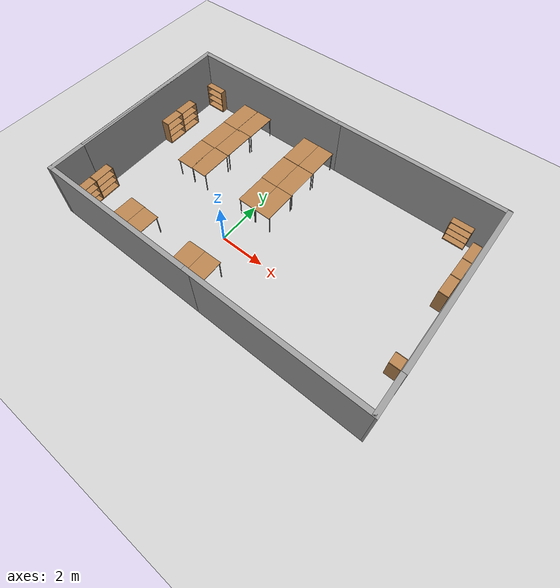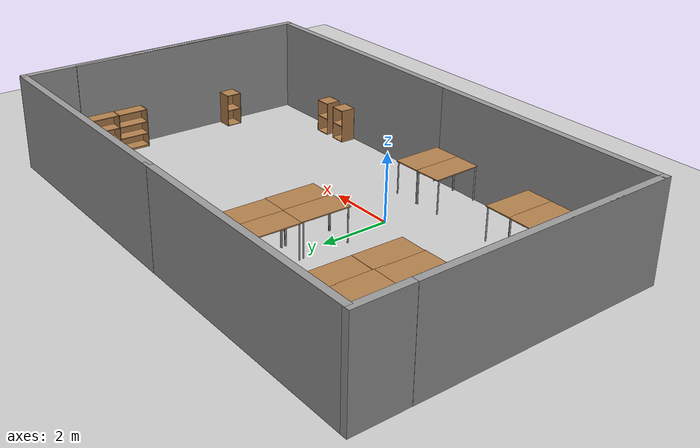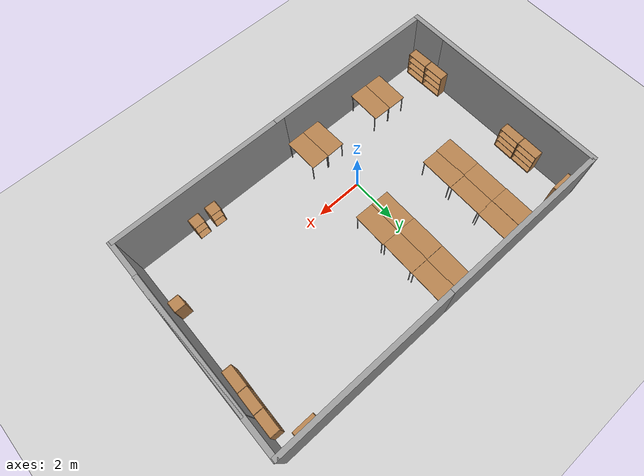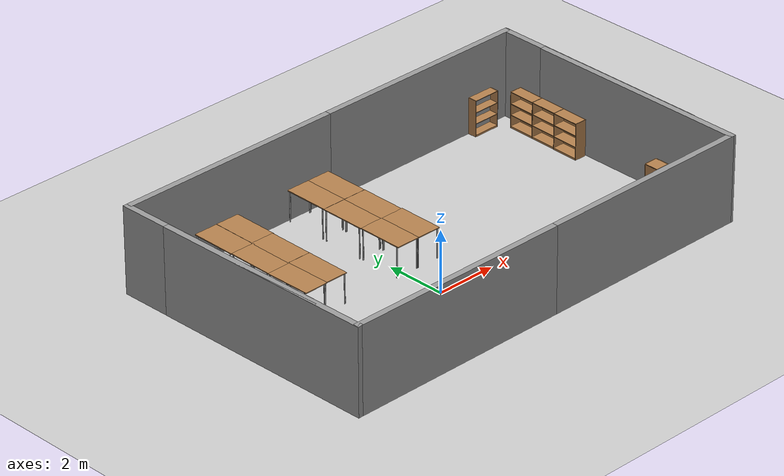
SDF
<sdf version="1.4">
 <world name="default">
  <light name="sun" type="directional">
   <pose>0 0 10 0 -0 0</pose>
   <diffuse>0.8 0.8 0.8 1</diffuse>
   <specular>0.2 0.2 0.2 1</specular>
   <attenuation>
    <range>1000</range>
    <constant>0.9</constant>
    <linear>0.01</linear>
    <quadratic>0.001</quadratic>
   </attenuation>
   <direction>-0.5 0.1 -0.9</direction>
  </light>
  <model name="ground_plane">
   <static>1</static>
   <link name="link">
    <collision name="collision">
     <geometry><plane><normal>0 0 1</normal><size>100 100</size></plane></geometry>
     <surface><friction><ode><mu>100</mu><mu2>50</mu2></ode></friction></surface>
    </collision>
    <visual name="visual">
     <cast_shadows>0</cast_shadows>
     <geometry><plane><normal>0 0 1</normal><size>100 100</size></plane></geometry>
     <material>
      <script><uri>file://media/materials/scripts/gazebo.material</uri><name>Gazebo/Grey</name></script>
     </material>
    </visual>
    <velocity_decay><linear>0</linear><angular>0</angular></velocity_decay>
   </link>
  </model>
  <physics type="ode">
   <max_step_size>0.001</max_step_size>
   <real_time_factor>1</real_time_factor>
   <real_time_update_rate>1000</real_time_update_rate>
   <gravity>0 0 -9.8</gravity>
  </physics>
  <scene><ambient>0.4 0.4 0.4 1</ambient><background>0.7 0.7 0.7 1</background><shadows>1</shadows></scene>
  <model name="grey_wall">
   <static>1</static>
   <link name="link">
    <pose>0 0 1.4 0 -0 0</pose>
    <collision name="collision"><geometry><box><size>7.5 0.2 2.8</size></box></geometry></collision>
    <visual name="visual">
     <cast_shadows>0</cast_shadows>
     <geometry><box><size>7.5 0.2 2.8</size></box></geometry>
     <material>
      <script>
       <uri>model://grey_wall/materials/scripts</uri>
       <uri>model://grey_wall/materials/textures</uri>
       <name>vrc/grey_wall</name>
      </script>
     </material>
    </visual>
    <velocity_decay><linear>0</linear><angular>0</angular></velocity_decay>
   </link>
   <pose>-2.2873 5.99729 0 0 -0 0</pose>
  </model>
  <model name="grey_wall_0">
   <static>1</static>
   <link name="link">
    <pose>0 0 1.4 0 -0 0</pose>
    <collision name="collision"><geometry><box><size>7.5 0.2 2.8</size></box></geometry></collision>
    <visual name="visual">
     <cast_shadows>0</cast_shadows>
     <geometry><box><size>7.5 0.2 2.8</size></box></geometry>
     <material>
      <script>
       <uri>model://grey_wall/materials/scripts</uri>
       <uri>model://grey_wall/materials/textures</uri>
       <name>vrc/grey_wall</name>
      </script>
     </material>
    </visual>
    <velocity_decay><linear>0</linear><angular>0</angular></velocity_decay>
   </link>
   <pose>5 6 0 0 -0 0</pose>
  </model>
  <model name="grey_wall_1">
   <static>1</static>
   <link name="link">
    <pose>0 0 1.4 0 -0 0</pose>
    <collision name="collision"><geometry><box><size>7.5 0.2 2.8</size></box></geometry></collision>
    <visual name="visual">
     <cast_shadows>0</cast_shadows>
     <geometry><box><size>7.5 0.2 2.8</size></box></geometry>
     <material>
      <script>
       <uri>model://grey_wall/materials/scripts</uri>
       <uri>model://grey_wall/materials/textures</uri>
       <name>vrc/grey_wall</name>
      </script>
     </material>
    </visual>
    <velocity_decay><linear>0</linear><angular>0</angular></velocity_decay>
   </link>
   <pose>-6.03141 2.34717 0 0 0 -1.56</pose>
  </model>
  <model name="grey_wall_2">
   <static>1</static>
   <link name="link">
    <pose>0 0 1.4 0 -0 0</pose>
    <collision name="collision"><geometry><box><size>7.5 0.2 2.8</size></box></geometry></collision>
    <visual name="visual">
     <cast_shadows>0</cast_shadows>
     <geometry><box><size>7.5 0.2 2.8</size></box></geometry>
     <material>
      <script>
       <uri>model://grey_wall/materials/scripts</uri>
       <uri>model://grey_wall/materials/textures</uri>
       <name>vrc/grey_wall</name>
      </script>
     </material>
    </visual>
    <velocity_decay><linear>0</linear><angular>0</angular></velocity_decay>
   </link>
   <pose>-6.01832 0.721265 0 0 0 -1.56</pose>
  </model>
  <model name="table">
   <static>1</static>
   <link name="link">
    <collision name="surface">
     <pose>0 0 1 0 -0 0</pose>
     <geometry><box><size>1.5 0.8 0.03</size></box></geometry>
     <surface><friction><ode><mu>0.6</mu><mu2>0.6</mu2></ode></friction></surface>
    </collision>
    <visual name="visual1">
     <pose>0 0 1 0 -0 0</pose>
     <geometry><box><size>1.5 0.8 0.03</size></box></geometry>
     <material>
      <script><uri>file://media/materials/scripts/gazebo.material</uri><name>Gazebo/Wood</name></script>
     </material>
    </visual>
    <collision name="front_left_leg">
     <pose>0.68 0.38 0.5 0 -0 0</pose>
     <geometry><cylinder><radius>0.02</radius><length>1</length></cylinder></geometry>
    </collision>
    <visual name="front_left_leg">
     <pose>0.68 0.38 0.5 0 -0 0</pose>
     <geometry><cylinder><radius>0.02</radius><length>1</length></cylinder></geometry>
     <material>
      <script><uri>file://media/materials/scripts/gazebo.material</uri><name>Gazebo/Grey</name></script>
     </material>
    </visual>
    <collision name="front_right_leg">
     <pose>0.68 -0.38 0.5 0 -0 0</pose>
     <geometry><cylinder><radius>0.02</radius><length>1</length></cylinder></geometry>
    </collision>
    <visual name="front_right_leg">
     <pose>0.68 -0.38 0.5 0 -0 0</pose>
     <geometry><cylinder><radius>0.02</radius><length>1</length></cylinder></geometry>
     <material>
      <script><uri>file://media/materials/scripts/gazebo.material</uri><name>Gazebo/Grey</name></script>
     </material>
    </visual>
    <collision name="back_right_leg">
     <pose>-0.68 -0.38 0.5 0 -0 0</pose>
     <geometry><cylinder><radius>0.02</radius><length>1</length></cylinder></geometry>
    </collision>
    <visual name="back_right_leg">
     <pose>-0.68 -0.38 0.5 0 -0 0</pose>
     <geometry><cylinder><radius>0.02</radius><length>1</length></cylinder></geometry>
     <material>
      <script><uri>file://media/materials/scripts/gazebo.material</uri><name>Gazebo/Grey</name></script>
     </material>
    </visual>
    <collision name="back_left_leg">
     <pose>-0.68 0.38 0.5 0 -0 0</pose>
     <geometry><cylinder><radius>0.02</radius><length>1</length></cylinder></geometry>
    </collision>
    <visual name="back_left_leg">
     <pose>-0.68 0.38 0.5 0 -0 0</pose>
     <geometry><cylinder><radius>0.02</radius><length>1</length></cylinder></geometry>
     <material>
      <script><uri>file://media/materials/scripts/gazebo.material</uri><name>Gazebo/Grey</name></script>
     </material>
    </visual>
    <velocity_decay><linear>0</linear><angular>0</angular></velocity_decay>
   </link>
   <pose>-3.39142 5.11799 0 0 -0 1.56319</pose>
  </model>
  <model name="table_0">
   <static>1</static>
   <link name="link">
    <collision name="surface">
     <pose>0 0 1 0 -0 0</pose>
     <geometry><box><size>1.5 0.8 0.03</size></box></geometry>
     <surface><friction><ode><mu>0.6</mu><mu2>0.6</mu2></ode></friction></surface>
    </collision>
    <visual name="visual1">
     <pose>0 0 1 0 -0 0</pose>
     <geometry><box><size>1.5 0.8 0.03</size></box></geometry>
     <material>
      <script><uri>file://media/materials/scripts/gazebo.material</uri><name>Gazebo/Wood</name></script>
     </material>
    </visual>
    <collision name="front_left_leg">
     <pose>0.68 0.38 0.5 0 -0 0</pose>
     <geometry><cylinder><radius>0.02</radius><length>1</length></cylinder></geometry>
    </collision>
    <visual name="front_left_leg">
     <pose>0.68 0.38 0.5 0 -0 0</pose>
     <geometry><cylinder><radius>0.02</radius><length>1</length></cylinder></geometry>
     <material>
      <script><uri>file://media/materials/scripts/gazebo.material</uri><name>Gazebo/Grey</name></script>
     </material>
    </visual>
    <collision name="front_right_leg">
     <pose>0.68 -0.38 0.5 0 -0 0</pose>
     <geometry><cylinder><radius>0.02</radius><length>1</length></cylinder></geometry>
    </collision>
    <visual name="front_right_leg">
     <pose>0.68 -0.38 0.5 0 -0 0</pose>
     <geometry><cylinder><radius>0.02</radius><length>1</length></cylinder></geometry>
     <material>
      <script><uri>file://media/materials/scripts/gazebo.material</uri><name>Gazebo/Grey</name></script>
     </material>
    </visual>
    <collision name="back_right_leg">
     <pose>-0.68 -0.38 0.5 0 -0 0</pose>
     <geometry><cylinder><radius>0.02</radius><length>1</length></cylinder></geometry>
    </collision>
    <visual name="back_right_leg">
     <pose>-0.68 -0.38 0.5 0 -0 0</pose>
     <geometry><cylinder><radius>0.02</radius><length>1</length></cylinder></geometry>
     <material>
      <script><uri>file://media/materials/scripts/gazebo.material</uri><name>Gazebo/Grey</name></script>
     </material>
    </visual>
    <collision name="back_left_leg">
     <pose>-0.68 0.38 0.5 0 -0 0</pose>
     <geometry><cylinder><radius>0.02</radius><length>1</length></cylinder></geometry>
    </collision>
    <visual name="back_left_leg">
     <pose>-0.68 0.38 0.5 0 -0 0</pose>
     <geometry><cylinder><radius>0.02</radius><length>1</length></cylinder></geometry>
     <material>
      <script><uri>file://media/materials/scripts/gazebo.material</uri><name>Gazebo/Grey</name></script>
     </material>
    </visual>
    <velocity_decay><linear>0</linear><angular>0</angular></velocity_decay>
   </link>
   <pose>-2.58708 5.11782 0 0 -0 1.56</pose>
  </model>
  <model name="table_1">
   <static>1</static>
   <link name="link">
    <collision name="surface">
     <pose>0 0 1 0 -0 0</pose>
     <geometry><box><size>1.5 0.8 0.03</size></box></geometry>
     <surface><friction><ode><mu>0.6</mu><mu2>0.6</mu2></ode></friction></surface>
    </collision>
    <visual name="visual1">
     <pose>0 0 1 0 -0 0</pose>
     <geometry><box><size>1.5 0.8 0.03</size></box></geometry>
     <material>
      <script><uri>file://media/materials/scripts/gazebo.material</uri><name>Gazebo/Wood</name></script>
     </material>
    </visual>
    <collision name="front_left_leg">
     <pose>0.68 0.38 0.5 0 -0 0</pose>
     <geometry><cylinder><radius>0.02</radius><length>1</length></cylinder></geometry>
    </collision>
    <visual name="front_left_leg">
     <pose>0.68 0.38 0.5 0 -0 0</pose>
     <geometry><cylinder><radius>0.02</radius><length>1</length></cylinder></geometry>
     <material>
      <script><uri>file://media/materials/scripts/gazebo.material</uri><name>Gazebo/Grey</name></script>
     </material>
    </visual>
    <collision name="front_right_leg">
     <pose>0.68 -0.38 0.5 0 -0 0</pose>
     <geometry><cylinder><radius>0.02</radius><length>1</length></cylinder></geometry>
    </collision>
    <visual name="front_right_leg">
     <pose>0.68 -0.38 0.5 0 -0 0</pose>
     <geometry><cylinder><radius>0.02</radius><length>1</length></cylinder></geometry>
     <material>
      <script><uri>file://media/materials/scripts/gazebo.material</uri><name>Gazebo/Grey</name></script>
     </material>
    </visual>
    <collision name="back_right_leg">
     <pose>-0.68 -0.38 0.5 0 -0 0</pose>
     <geometry><cylinder><radius>0.02</radius><length>1</length></cylinder></geometry>
    </collision>
    <visual name="back_right_leg">
     <pose>-0.68 -0.38 0.5 0 -0 0</pose>
     <geometry><cylinder><radius>0.02</radius><length>1</length></cylinder></geometry>
     <material>
      <script><uri>file://media/materials/scripts/gazebo.material</uri><name>Gazebo/Grey</name></script>
     </material>
    </visual>
    <collision name="back_left_leg">
     <pose>-0.68 0.38 0.5 0 -0 0</pose>
     <geometry><cylinder><radius>0.02</radius><length>1</length></cylinder></geometry>
    </collision>
    <visual name="back_left_leg">
     <pose>-0.68 0.38 0.5 0 -0 0</pose>
     <geometry><cylinder><radius>0.02</radius><length>1</length></cylinder></geometry>
     <material>
      <script><uri>file://media/materials/scripts/gazebo.material</uri><name>Gazebo/Grey</name></script>
     </material>
    </visual>
    <velocity_decay><linear>0</linear><angular>0</angular></velocity_decay>
   </link>
   <pose>-3.39295 3.62708 0 0 -0 1.56</pose>
  </model>
  <model name="table_2">
   <static>1</static>
   <link name="link">
    <collision name="surface">
     <pose>0 0 1 0 -0 0</pose>
     <geometry><box><size>1.5 0.8 0.03</size></box></geometry>
     <surface><friction><ode><mu>0.6</mu><mu2>0.6</mu2></ode></friction></surface>
    </collision>
    <visual name="visual1">
     <pose>0 0 1 0 -0 0</pose>
     <geometry><box><size>1.5 0.8 0.03</size></box></geometry>
     <material>
      <script><uri>file://media/materials/scripts/gazebo.material</uri><name>Gazebo/Wood</name></script>
     </material>
    </visual>
    <collision name="front_left_leg">
     <pose>0.68 0.38 0.5 0 -0 0</pose>
     <geometry><cylinder><radius>0.02</radius><length>1</length></cylinder></geometry>
    </collision>
    <visual name="front_left_leg">
     <pose>0.68 0.38 0.5 0 -0 0</pose>
     <geometry><cylinder><radius>0.02</radius><length>1</length></cylinder></geometry>
     <material>
      <script><uri>file://media/materials/scripts/gazebo.material</uri><name>Gazebo/Grey</name></script>
     </material>
    </visual>
    <collision name="front_right_leg">
     <pose>0.68 -0.38 0.5 0 -0 0</pose>
     <geometry><cylinder><radius>0.02</radius><length>1</length></cylinder></geometry>
    </collision>
    <visual name="front_right_leg">
     <pose>0.68 -0.38 0.5 0 -0 0</pose>
     <geometry><cylinder><radius>0.02</radius><length>1</length></cylinder></geometry>
     <material>
      <script><uri>file://media/materials/scripts/gazebo.material</uri><name>Gazebo/Grey</name></script>
     </material>
    </visual>
    <collision name="back_right_leg">
     <pose>-0.68 -0.38 0.5 0 -0 0</pose>
     <geometry><cylinder><radius>0.02</radius><length>1</length></cylinder></geometry>
    </collision>
    <visual name="back_right_leg">
     <pose>-0.68 -0.38 0.5 0 -0 0</pose>
     <geometry><cylinder><radius>0.02</radius><length>1</length></cylinder></geometry>
     <material>
      <script><uri>file://media/materials/scripts/gazebo.material</uri><name>Gazebo/Grey</name></script>
     </material>
    </visual>
    <collision name="back_left_leg">
     <pose>-0.68 0.38 0.5 0 -0 0</pose>
     <geometry><cylinder><radius>0.02</radius><length>1</length></cylinder></geometry>
    </collision>
    <visual name="back_left_leg">
     <pose>-0.68 0.38 0.5 0 -0 0</pose>
     <geometry><cylinder><radius>0.02</radius><length>1</length></cylinder></geometry>
     <material>
      <script><uri>file://media/materials/scripts/gazebo.material</uri><name>Gazebo/Grey</name></script>
     </material>
    </visual>
    <velocity_decay><linear>0</linear><angular>0</angular></velocity_decay>
   </link>
   <pose>-2.62064 3.65825 0 0 -0 1.56</pose>
  </model>
  <model name="table_3">
   <static>1</static>
   <link name="link">
    <collision name="surface">
     <pose>0 0 1 0 -0 0</pose>
     <geometry><box><size>1.5 0.8 0.03</size></box></geometry>
     <surface><friction><ode><mu>0.6</mu><mu2>0.6</mu2></ode></friction></surface>
    </collision>
    <visual name="visual1">
     <pose>0 0 1 0 -0 0</pose>
     <geometry><box><size>1.5 0.8 0.03</size></box></geometry>
     <material>
      <script><uri>file://media/materials/scripts/gazebo.material</uri><name>Gazebo/Wood</name></script>
     </material>
    </visual>
    <collision name="front_left_leg">
     <pose>0.68 0.38 0.5 0 -0 0</pose>
     <geometry><cylinder><radius>0.02</radius><length>1</length></cylinder></geometry>
    </collision>
    <visual name="front_left_leg">
     <pose>0.68 0.38 0.5 0 -0 0</pose>
     <geometry><cylinder><radius>0.02</radius><length>1</length></cylinder></geometry>
     <material>
      <script><uri>file://media/materials/scripts/gazebo.material</uri><name>Gazebo/Grey</name></script>
     </material>
    </visual>
    <collision name="front_right_leg">
     <pose>0.68 -0.38 0.5 0 -0 0</pose>
     <geometry><cylinder><radius>0.02</radius><length>1</length></cylinder></geometry>
    </collision>
    <visual name="front_right_leg">
     <pose>0.68 -0.38 0.5 0 -0 0</pose>
     <geometry><cylinder><radius>0.02</radius><length>1</length></cylinder></geometry>
     <material>
      <script><uri>file://media/materials/scripts/gazebo.material</uri><name>Gazebo/Grey</name></script>
     </material>
    </visual>
    <collision name="back_right_leg">
     <pose>-0.68 -0.38 0.5 0 -0 0</pose>
     <geometry><cylinder><radius>0.02</radius><length>1</length></cylinder></geometry>
    </collision>
    <visual name="back_right_leg">
     <pose>-0.68 -0.38 0.5 0 -0 0</pose>
     <geometry><cylinder><radius>0.02</radius><length>1</length></cylinder></geometry>
     <material>
      <script><uri>file://media/materials/scripts/gazebo.material</uri><name>Gazebo/Grey</name></script>
     </material>
    </visual>
    <collision name="back_left_leg">
     <pose>-0.68 0.38 0.5 0 -0 0</pose>
     <geometry><cylinder><radius>0.02</radius><length>1</length></cylinder></geometry>
    </collision>
    <visual name="back_left_leg">
     <pose>-0.68 0.38 0.5 0 -0 0</pose>
     <geometry><cylinder><radius>0.02</radius><length>1</length></cylinder></geometry>
     <material>
      <script><uri>file://media/materials/scripts/gazebo.material</uri><name>Gazebo/Grey</name></script>
     </material>
    </visual>
    <velocity_decay><linear>0</linear><angular>0</angular></velocity_decay>
   </link>
   <pose>-3.40002 2.13471 0 0 0 -1.56</pose>
  </model>
  <model name="table_4">
   <static>1</static>
   <link name="link">
    <collision name="surface">
     <pose>0 0 1 0 -0 0</pose>
     <geometry><box><size>1.5 0.8 0.03</size></box></geometry>
     <surface><friction><ode><mu>0.6</mu><mu2>0.6</mu2></ode></friction></surface>
    </collision>
    <visual name="visual1">
     <pose>0 0 1 0 -0 0</pose>
     <geometry><box><size>1.5 0.8 0.03</size></box></geometry>
     <material>
      <script><uri>file://media/materials/scripts/gazebo.material</uri><name>Gazebo/Wood</name></script>
     </material>
    </visual>
    <collision name="front_left_leg">
     <pose>0.68 0.38 0.5 0 -0 0</pose>
     <geometry><cylinder><radius>0.02</radius><length>1</length></cylinder></geometry>
    </collision>
    <visual name="front_left_leg">
     <pose>0.68 0.38 0.5 0 -0 0</pose>
     <geometry><cylinder><radius>0.02</radius><length>1</length></cylinder></geometry>
     <material>
      <script><uri>file://media/materials/scripts/gazebo.material</uri><name>Gazebo/Grey</name></script>
     </material>
    </visual>
    <collision name="front_right_leg">
     <pose>0.68 -0.38 0.5 0 -0 0</pose>
     <geometry><cylinder><radius>0.02</radius><length>1</length></cylinder></geometry>
    </collision>
    <visual name="front_right_leg">
     <pose>0.68 -0.38 0.5 0 -0 0</pose>
     <geometry><cylinder><radius>0.02</radius><length>1</length></cylinder></geometry>
     <material>
      <script><uri>file://media/materials/scripts/gazebo.material</uri><name>Gazebo/Grey</name></script>
     </material>
    </visual>
    <collision name="back_right_leg">
     <pose>-0.68 -0.38 0.5 0 -0 0</pose>
     <geometry><cylinder><radius>0.02</radius><length>1</length></cylinder></geometry>
    </collision>
    <visual name="back_right_leg">
     <pose>-0.68 -0.38 0.5 0 -0 0</pose>
     <geometry><cylinder><radius>0.02</radius><length>1</length></cylinder></geometry>
     <material>
      <script><uri>file://media/materials/scripts/gazebo.material</uri><name>Gazebo/Grey</name></script>
     </material>
    </visual>
    <collision name="back_left_leg">
     <pose>-0.68 0.38 0.5 0 -0 0</pose>
     <geometry><cylinder><radius>0.02</radius><length>1</length></cylinder></geometry>
    </collision>
    <visual name="back_left_leg">
     <pose>-0.68 0.38 0.5 0 -0 0</pose>
     <geometry><cylinder><radius>0.02</radius><length>1</length></cylinder></geometry>
     <material>
      <script><uri>file://media/materials/scripts/gazebo.material</uri><name>Gazebo/Grey</name></script>
     </material>
    </visual>
    <velocity_decay><linear>0</linear><angular>0</angular></velocity_decay>
   </link>
   <pose>-2.63477 2.15257 0 0 -0 1.56</pose>
  </model>
  <model name="table_5">
   <static>1</static>
   <link name="link">
    <collision name="surface">
     <pose>0 0 1 0 -0 0</pose>
     <geometry><box><size>1.5 0.8 0.03</size></box></geometry>
     <surface><friction><ode><mu>0.6</mu><mu2>0.6</mu2></ode></friction></surface>
    </collision>
    <visual name="visual1">
     <pose>0 0 1 0 -0 0</pose>
     <geometry><box><size>1.5 0.8 0.03</size></box></geometry>
     <material>
      <script><uri>file://media/materials/scripts/gazebo.material</uri><name>Gazebo/Wood</name></script>
     </material>
    </visual>
    <collision name="front_left_leg">
     <pose>0.68 0.38 0.5 0 -0 0</pose>
     <geometry><cylinder><radius>0.02</radius><length>1</length></cylinder></geometry>
    </collision>
    <visual name="front_left_leg">
     <pose>0.68 0.38 0.5 0 -0 0</pose>
     <geometry><cylinder><radius>0.02</radius><length>1</length></cylinder></geometry>
     <material>
      <script><uri>file://media/materials/scripts/gazebo.material</uri><name>Gazebo/Grey</name></script>
     </material>
    </visual>
    <collision name="front_right_leg">
     <pose>0.68 -0.38 0.5 0 -0 0</pose>
     <geometry><cylinder><radius>0.02</radius><length>1</length></cylinder></geometry>
    </collision>
    <visual name="front_right_leg">
     <pose>0.68 -0.38 0.5 0 -0 0</pose>
     <geometry><cylinder><radius>0.02</radius><length>1</length></cylinder></geometry>
     <material>
      <script><uri>file://media/materials/scripts/gazebo.material</uri><name>Gazebo/Grey</name></script>
     </material>
    </visual>
    <collision name="back_right_leg">
     <pose>-0.68 -0.38 0.5 0 -0 0</pose>
     <geometry><cylinder><radius>0.02</radius><length>1</length></cylinder></geometry>
    </collision>
    <visual name="back_right_leg">
     <pose>-0.68 -0.38 0.5 0 -0 0</pose>
     <geometry><cylinder><radius>0.02</radius><length>1</length></cylinder></geometry>
     <material>
      <script><uri>file://media/materials/scripts/gazebo.material</uri><name>Gazebo/Grey</name></script>
     </material>
    </visual>
    <collision name="back_left_leg">
     <pose>-0.68 0.38 0.5 0 -0 0</pose>
     <geometry><cylinder><radius>0.02</radius><length>1</length></cylinder></geometry>
    </collision>
    <visual name="back_left_leg">
     <pose>-0.68 0.38 0.5 0 -0 0</pose>
     <geometry><cylinder><radius>0.02</radius><length>1</length></cylinder></geometry>
     <material>
      <script><uri>file://media/materials/scripts/gazebo.material</uri><name>Gazebo/Grey</name></script>
     </material>
    </visual>
    <velocity_decay><linear>0</linear><angular>0</angular></velocity_decay>
   </link>
   <pose>0.132371 5.12025 0 0 -0 1.56</pose>
  </model>
  <model name="table_6">
   <static>1</static>
   <link name="link">
    <collision name="surface">
     <pose>0 0 1 0 -0 0</pose>
     <geometry><box><size>1.5 0.8 0.03</size></box></geometry>
     <surface><friction><ode><mu>0.6</mu><mu2>0.6</mu2></ode></friction></surface>
    </collision>
    <visual name="visual1">
     <pose>0 0 1 0 -0 0</pose>
     <geometry><box><size>1.5 0.8 0.03</size></box></geometry>
     <material>
      <script><uri>file://media/materials/scripts/gazebo.material</uri><name>Gazebo/Wood</name></script>
     </material>
    </visual>
    <collision name="front_left_leg">
     <pose>0.68 0.38 0.5 0 -0 0</pose>
     <geometry><cylinder><radius>0.02</radius><length>1</length></cylinder></geometry>
    </collision>
    <visual name="front_left_leg">
     <pose>0.68 0.38 0.5 0 -0 0</pose>
     <geometry><cylinder><radius>0.02</radius><length>1</length></cylinder></geometry>
     <material>
      <script><uri>file://media/materials/scripts/gazebo.material</uri><name>Gazebo/Grey</name></script>
     </material>
    </visual>
    <collision name="front_right_leg">
     <pose>0.68 -0.38 0.5 0 -0 0</pose>
     <geometry><cylinder><radius>0.02</radius><length>1</length></cylinder></geometry>
    </collision>
    <visual name="front_right_leg">
     <pose>0.68 -0.38 0.5 0 -0 0</pose>
     <geometry><cylinder><radius>0.02</radius><length>1</length></cylinder></geometry>
     <material>
      <script><uri>file://media/materials/scripts/gazebo.material</uri><name>Gazebo/Grey</name></script>
     </material>
    </visual>
    <collision name="back_right_leg">
     <pose>-0.68 -0.38 0.5 0 -0 0</pose>
     <geometry><cylinder><radius>0.02</radius><length>1</length></cylinder></geometry>
    </collision>
    <visual name="back_right_leg">
     <pose>-0.68 -0.38 0.5 0 -0 0</pose>
     <geometry><cylinder><radius>0.02</radius><length>1</length></cylinder></geometry>
     <material>
      <script><uri>file://media/materials/scripts/gazebo.material</uri><name>Gazebo/Grey</name></script>
     </material>
    </visual>
    <collision name="back_left_leg">
     <pose>-0.68 0.38 0.5 0 -0 0</pose>
     <geometry><cylinder><radius>0.02</radius><length>1</length></cylinder></geometry>
    </collision>
    <visual name="back_left_leg">
     <pose>-0.68 0.38 0.5 0 -0 0</pose>
     <geometry><cylinder><radius>0.02</radius><length>1</length></cylinder></geometry>
     <material>
      <script><uri>file://media/materials/scripts/gazebo.material</uri><name>Gazebo/Grey</name></script>
     </material>
    </visual>
    <velocity_decay><linear>0</linear><angular>0</angular></velocity_decay>
   </link>
   <pose>0.911696 5.11618 0 0 -0 1.56</pose>
  </model>
  <model name="table_7">
   <static>1</static>
   <link name="link">
    <collision name="surface">
     <pose>0 0 1 0 -0 0</pose>
     <geometry><box><size>1.5 0.8 0.03</size></box></geometry>
     <surface><friction><ode><mu>0.6</mu><mu2>0.6</mu2></ode></friction></surface>
    </collision>
    <visual name="visual1">
     <pose>0 0 1 0 -0 0</pose>
     <geometry><box><size>1.5 0.8 0.03</size></box></geometry>
     <material>
      <script><uri>file://media/materials/scripts/gazebo.material</uri><name>Gazebo/Wood</name></script>
     </material>
    </visual>
    <collision name="front_left_leg">
     <pose>0.68 0.38 0.5 0 -0 0</pose>
     <geometry><cylinder><radius>0.02</radius><length>1</length></cylinder></geometry>
    </collision>
    <visual name="front_left_leg">
     <pose>0.68 0.38 0.5 0 -0 0</pose>
     <geometry><cylinder><radius>0.02</radius><length>1</length></cylinder></geometry>
     <material>
      <script><uri>file://media/materials/scripts/gazebo.material</uri><name>Gazebo/Grey</name></script>
     </material>
    </visual>
    <collision name="front_right_leg">
     <pose>0.68 -0.38 0.5 0 -0 0</pose>
     <geometry><cylinder><radius>0.02</radius><length>1</length></cylinder></geometry>
    </collision>
    <visual name="front_right_leg">
     <pose>0.68 -0.38 0.5 0 -0 0</pose>
     <geometry><cylinder><radius>0.02</radius><length>1</length></cylinder></geometry>
     <material>
      <script><uri>file://media/materials/scripts/gazebo.material</uri><name>Gazebo/Grey</name></script>
     </material>
    </visual>
    <collision name="back_right_leg">
     <pose>-0.68 -0.38 0.5 0 -0 0</pose>
     <geometry><cylinder><radius>0.02</radius><length>1</length></cylinder></geometry>
    </collision>
    <visual name="back_right_leg">
     <pose>-0.68 -0.38 0.5 0 -0 0</pose>
     <geometry><cylinder><radius>0.02</radius><length>1</length></cylinder></geometry>
     <material>
      <script><uri>file://media/materials/scripts/gazebo.material</uri><name>Gazebo/Grey</name></script>
     </material>
    </visual>
    <collision name="back_left_leg">
     <pose>-0.68 0.38 0.5 0 -0 0</pose>
     <geometry><cylinder><radius>0.02</radius><length>1</length></cylinder></geometry>
    </collision>
    <visual name="back_left_leg">
     <pose>-0.68 0.38 0.5 0 -0 0</pose>
     <geometry><cylinder><radius>0.02</radius><length>1</length></cylinder></geometry>
     <material>
      <script><uri>file://media/materials/scripts/gazebo.material</uri><name>Gazebo/Grey</name></script>
     </material>
    </visual>
    <velocity_decay><linear>0</linear><angular>0</angular></velocity_decay>
   </link>
   <pose>0.111052 3.61177 0 0 -0 1.56</pose>
  </model>
  <model name="table_8">
   <static>1</static>
   <link name="link">
    <collision name="surface">
     <pose>0 0 1 0 -0 0</pose>
     <geometry><box><size>1.5 0.8 0.03</size></box></geometry>
     <surface><friction><ode><mu>0.6</mu><mu2>0.6</mu2></ode></friction></surface>
    </collision>
    <visual name="visual1">
     <pose>0 0 1 0 -0 0</pose>
     <geometry><box><size>1.5 0.8 0.03</size></box></geometry>
     <material>
      <script><uri>file://media/materials/scripts/gazebo.material</uri><name>Gazebo/Wood</name></script>
     </material>
    </visual>
    <collision name="front_left_leg">
     <pose>0.68 0.38 0.5 0 -0 0</pose>
     <geometry><cylinder><radius>0.02</radius><length>1</length></cylinder></geometry>
    </collision>
    <visual name="front_left_leg">
     <pose>0.68 0.38 0.5 0 -0 0</pose>
     <geometry><cylinder><radius>0.02</radius><length>1</length></cylinder></geometry>
     <material>
      <script><uri>file://media/materials/scripts/gazebo.material</uri><name>Gazebo/Grey</name></script>
     </material>
    </visual>
    <collision name="front_right_leg">
     <pose>0.68 -0.38 0.5 0 -0 0</pose>
     <geometry><cylinder><radius>0.02</radius><length>1</length></cylinder></geometry>
    </collision>
    <visual name="front_right_leg">
     <pose>0.68 -0.38 0.5 0 -0 0</pose>
     <geometry><cylinder><radius>0.02</radius><length>1</length></cylinder></geometry>
     <material>
      <script><uri>file://media/materials/scripts/gazebo.material</uri><name>Gazebo/Grey</name></script>
     </material>
    </visual>
    <collision name="back_right_leg">
     <pose>-0.68 -0.38 0.5 0 -0 0</pose>
     <geometry><cylinder><radius>0.02</radius><length>1</length></cylinder></geometry>
    </collision>
    <visual name="back_right_leg">
     <pose>-0.68 -0.38 0.5 0 -0 0</pose>
     <geometry><cylinder><radius>0.02</radius><length>1</length></cylinder></geometry>
     <material>
      <script><uri>file://media/materials/scripts/gazebo.material</uri><name>Gazebo/Grey</name></script>
     </material>
    </visual>
    <collision name="back_left_leg">
     <pose>-0.68 0.38 0.5 0 -0 0</pose>
     <geometry><cylinder><radius>0.02</radius><length>1</length></cylinder></geometry>
    </collision>
    <visual name="back_left_leg">
     <pose>-0.68 0.38 0.5 0 -0 0</pose>
     <geometry><cylinder><radius>0.02</radius><length>1</length></cylinder></geometry>
     <material>
      <script><uri>file://media/materials/scripts/gazebo.material</uri><name>Gazebo/Grey</name></script>
     </material>
    </visual>
    <velocity_decay><linear>0</linear><angular>0</angular></velocity_decay>
   </link>
   <pose>0.901342 3.61101 0 0 -0 1.56</pose>
  </model>
  <model name="table_9">
   <static>1</static>
   <link name="link">
    <collision name="surface">
     <pose>0 0 1 0 -0 0</pose>
     <geometry><box><size>1.5 0.8 0.03</size></box></geometry>
     <surface><friction><ode><mu>0.6</mu><mu2>0.6</mu2></ode></friction></surface>
    </collision>
    <visual name="visual1">
     <pose>0 0 1 0 -0 0</pose>
     <geometry><box><size>1.5 0.8 0.03</size></box></geometry>
     <material>
      <script><uri>file://media/materials/scripts/gazebo.material</uri><name>Gazebo/Wood</name></script>
     </material>
    </visual>
    <collision name="front_left_leg">
     <pose>0.68 0.38 0.5 0 -0 0</pose>
     <geometry><cylinder><radius>0.02</radius><length>1</length></cylinder></geometry>
    </collision>
    <visual name="front_left_leg">
     <pose>0.68 0.38 0.5 0 -0 0</pose>
     <geometry><cylinder><radius>0.02</radius><length>1</length></cylinder></geometry>
     <material>
      <script><uri>file://media/materials/scripts/gazebo.material</uri><name>Gazebo/Grey</name></script>
     </material>
    </visual>
    <collision name="front_right_leg">
     <pose>0.68 -0.38 0.5 0 -0 0</pose>
     <geometry><cylinder><radius>0.02</radius><length>1</length></cylinder></geometry>
    </collision>
    <visual name="front_right_leg">
     <pose>0.68 -0.38 0.5 0 -0 0</pose>
     <geometry><cylinder><radius>0.02</radius><length>1</length></cylinder></geometry>
     <material>
      <script><uri>file://media/materials/scripts/gazebo.material</uri><name>Gazebo/Grey</name></script>
     </material>
    </visual>
    <collision name="back_right_leg">
     <pose>-0.68 -0.38 0.5 0 -0 0</pose>
     <geometry><cylinder><radius>0.02</radius><length>1</length></cylinder></geometry>
    </collision>
    <visual name="back_right_leg">
     <pose>-0.68 -0.38 0.5 0 -0 0</pose>
     <geometry><cylinder><radius>0.02</radius><length>1</length></cylinder></geometry>
     <material>
      <script><uri>file://media/materials/scripts/gazebo.material</uri><name>Gazebo/Grey</name></script>
     </material>
    </visual>
    <collision name="back_left_leg">
     <pose>-0.68 0.38 0.5 0 -0 0</pose>
     <geometry><cylinder><radius>0.02</radius><length>1</length></cylinder></geometry>
    </collision>
    <visual name="back_left_leg">
     <pose>-0.68 0.38 0.5 0 -0 0</pose>
     <geometry><cylinder><radius>0.02</radius><length>1</length></cylinder></geometry>
     <material>
      <script><uri>file://media/materials/scripts/gazebo.material</uri><name>Gazebo/Grey</name></script>
     </material>
    </visual>
    <velocity_decay><linear>0</linear><angular>0</angular></velocity_decay>
   </link>
   <pose>0.113272 2.1269 0 0 -0 1.56</pose>
  </model>
  <model name="table_10">
   <static>1</static>
   <link name="link">
    <collision name="surface">
     <pose>0 0 1 0 -0 0</pose>
     <geometry><box><size>1.5 0.8 0.03</size></box></geometry>
     <surface><friction><ode><mu>0.6</mu><mu2>0.6</mu2></ode></friction></surface>
    </collision>
    <visual name="visual1">
     <pose>0 0 1 0 -0 0</pose>
     <geometry><box><size>1.5 0.8 0.03</size></box></geometry>
     <material>
      <script><uri>file://media/materials/scripts/gazebo.material</uri><name>Gazebo/Wood</name></script>
     </material>
    </visual>
    <collision name="front_left_leg">
     <pose>0.68 0.38 0.5 0 -0 0</pose>
     <geometry><cylinder><radius>0.02</radius><length>1</length></cylinder></geometry>
    </collision>
    <visual name="front_left_leg">
     <pose>0.68 0.38 0.5 0 -0 0</pose>
     <geometry><cylinder><radius>0.02</radius><length>1</length></cylinder></geometry>
     <material>
      <script><uri>file://media/materials/scripts/gazebo.material</uri><name>Gazebo/Grey</name></script>
     </material>
    </visual>
    <collision name="front_right_leg">
     <pose>0.68 -0.38 0.5 0 -0 0</pose>
     <geometry><cylinder><radius>0.02</radius><length>1</length></cylinder></geometry>
    </collision>
    <visual name="front_right_leg">
     <pose>0.68 -0.38 0.5 0 -0 0</pose>
     <geometry><cylinder><radius>0.02</radius><length>1</length></cylinder></geometry>
     <material>
      <script><uri>file://media/materials/scripts/gazebo.material</uri><name>Gazebo/Grey</name></script>
     </material>
    </visual>
    <collision name="back_right_leg">
     <pose>-0.68 -0.38 0.5 0 -0 0</pose>
     <geometry><cylinder><radius>0.02</radius><length>1</length></cylinder></geometry>
    </collision>
    <visual name="back_right_leg">
     <pose>-0.68 -0.38 0.5 0 -0 0</pose>
     <geometry><cylinder><radius>0.02</radius><length>1</length></cylinder></geometry>
     <material>
      <script><uri>file://media/materials/scripts/gazebo.material</uri><name>Gazebo/Grey</name></script>
     </material>
    </visual>
    <collision name="back_left_leg">
     <pose>-0.68 0.38 0.5 0 -0 0</pose>
     <geometry><cylinder><radius>0.02</radius><length>1</length></cylinder></geometry>
    </collision>
    <visual name="back_left_leg">
     <pose>-0.68 0.38 0.5 0 -0 0</pose>
     <geometry><cylinder><radius>0.02</radius><length>1</length></cylinder></geometry>
     <material>
      <script><uri>file://media/materials/scripts/gazebo.material</uri><name>Gazebo/Grey</name></script>
     </material>
    </visual>
    <velocity_decay><linear>0</linear><angular>0</angular></velocity_decay>
   </link>
   <pose>0.912943 2.11882 0 0 -0 1.56</pose>
  </model>
  <model name="bookshelf">
   <static>1</static>
   <link name="link">
    <inertial><mass>1</mass></inertial>
    <collision name="back">
     <pose>0 0.005 0.6 0 -0 0</pose>
     <geometry><box><size>0.9 0.01 1.2</size></box></geometry>
    </collision>
    <visual name="visual1">
     <pose>0 0.005 0.6 0 -0 0</pose>
     <geometry><box><size>0.9 0.01 1.2</size></box></geometry>
     <material>
      <script><uri>file://media/materials/scripts/gazebo.material</uri><name>Gazebo/Wood</name></script>
     </material>
    </visual>
    <collision name="left_side">
     <pose>0.45 -0.195 0.6 0 -0 0</pose>
     <geometry><box><size>0.02 0.4 1.2</size></box></geometry>
    </collision>
    <visual name="visual2">
     <pose>0.45 -0.195 0.6 0 -0 0</pose>
     <geometry><box><size>0.02 0.4 1.2</size></box></geometry>
     <material>
      <script><uri>file://media/materials/scripts/gazebo.material</uri><name>Gazebo/Wood</name></script>
     </material>
    </visual>
    <collision name="right_side">
     <pose>-0.45 -0.195 0.6 0 -0 0</pose>
     <geometry><box><size>0.02 0.4 1.2</size></box></geometry>
    </collision>
    <visual name="visual3">
     <pose>-0.45 -0.195 0.6 0 -0 0</pose>
     <geometry><box><size>0.02 0.4 1.2</size></box></geometry>
     <material>
      <script><uri>file://media/materials/scripts/gazebo.material</uri><name>Gazebo/Wood</name></script>
     </material>
    </visual>
    <collision name="bottom">
     <pose>0 -0.195 0.03 0 -0 0</pose>
     <geometry><box><size>0.88 0.4 0.06</size></box></geometry>
    </collision>
    <visual name="visual4">
     <pose>0 -0.195 0.03 0 -0 0</pose>
     <geometry><box><size>0.88 0.4 0.06</size></box></geometry>
     <material>
      <script><uri>file://media/materials/scripts/gazebo.material</uri><name>Gazebo/Wood</name></script>
     </material>
    </visual>
    <collision name="top">
     <pose>0 -0.195 1.19 0 -0 0</pose>
     <geometry><box><size>0.88 0.4 0.02</size></box></geometry>
    </collision>
    <visual name="visual5">
     <pose>0 -0.195 1.19 0 -0 0</pose>
     <geometry><box><size>0.88 0.4 0.02</size></box></geometry>
     <material>
      <script><uri>file://media/materials/scripts/gazebo.material</uri><name>Gazebo/Wood</name></script>
     </material>
    </visual>
    <collision name="low_shelf">
     <pose>0 -0.195 0.43 0 -0 0</pose>
     <geometry><box><size>0.88 0.4 0.02</size></box></geometry>
    </collision>
    <visual name="visual6">
     <pose>0 -0.195 0.43 0 -0 0</pose>
     <geometry><box><size>0.88 0.4 0.02</size></box></geometry>
     <material>
      <script><uri>file://media/materials/scripts/gazebo.material</uri><name>Gazebo/Wood</name></script>
     </material>
    </visual>
    <collision name="high_shelf">
     <pose>0 -0.195 0.8 0 -0 0</pose>
     <geometry><box><size>0.88 0.4 0.02</size></box></geometry>
    </collision>
    <visual name="visual7">
     <pose>0 -0.195 0.8 0 -0 0</pose>
     <geometry><box><size>0.88 0.4 0.02</size></box></geometry>
     <material>
      <script><uri>file://media/materials/scripts/gazebo.material</uri><name>Gazebo/Wood</name></script>
     </material>
    </visual>
    <velocity_decay><linear>0</linear><angular>0</angular></velocity_decay>
   </link>
   <pose>-5.83555 -2.19567 0 0 -0 1.6</pose>
  </model>
  <model name="bookshelf_0">
   <static>1</static>
   <link name="link">
    <inertial><mass>1</mass></inertial>
    <collision name="back">
     <pose>0 0.005 0.6 0 -0 0</pose>
     <geometry><box><size>0.9 0.01 1.2</size></box></geometry>
    </collision>
    <visual name="visual1">
     <pose>0 0.005 0.6 0 -0 0</pose>
     <geometry><box><size>0.9 0.01 1.2</size></box></geometry>
     <material>
      <script><uri>file://media/materials/scripts/gazebo.material</uri><name>Gazebo/Wood</name></script>
     </material>
    </visual>
    <collision name="left_side">
     <pose>0.45 -0.195 0.6 0 -0 0</pose>
     <geometry><box><size>0.02 0.4 1.2</size></box></geometry>
    </collision>
    <visual name="visual2">
     <pose>0.45 -0.195 0.6 0 -0 0</pose>
     <geometry><box><size>0.02 0.4 1.2</size></box></geometry>
     <material>
      <script><uri>file://media/materials/scripts/gazebo.material</uri><name>Gazebo/Wood</name></script>
     </material>
    </visual>
    <collision name="right_side">
     <pose>-0.45 -0.195 0.6 0 -0 0</pose>
     <geometry><box><size>0.02 0.4 1.2</size></box></geometry>
    </collision>
    <visual name="visual3">
     <pose>-0.45 -0.195 0.6 0 -0 0</pose>
     <geometry><box><size>0.02 0.4 1.2</size></box></geometry>
     <material>
      <script><uri>file://media/materials/scripts/gazebo.material</uri><name>Gazebo/Wood</name></script>
     </material>
    </visual>
    <collision name="bottom">
     <pose>0 -0.195 0.03 0 -0 0</pose>
     <geometry><box><size>0.88 0.4 0.06</size></box></geometry>
    </collision>
    <visual name="visual4">
     <pose>0 -0.195 0.03 0 -0 0</pose>
     <geometry><box><size>0.88 0.4 0.06</size></box></geometry>
     <material>
      <script><uri>file://media/materials/scripts/gazebo.material</uri><name>Gazebo/Wood</name></script>
     </material>
    </visual>
    <collision name="top">
     <pose>0 -0.195 1.19 0 -0 0</pose>
     <geometry><box><size>0.88 0.4 0.02</size></box></geometry>
    </collision>
    <visual name="visual5">
     <pose>0 -0.195 1.19 0 -0 0</pose>
     <geometry><box><size>0.88 0.4 0.02</size></box></geometry>
     <material>
      <script><uri>file://media/materials/scripts/gazebo.material</uri><name>Gazebo/Wood</name></script>
     </material>
    </visual>
    <collision name="low_shelf">
     <pose>0 -0.195 0.43 0 -0 0</pose>
     <geometry><box><size>0.88 0.4 0.02</size></box></geometry>
    </collision>
    <visual name="visual6">
     <pose>0 -0.195 0.43 0 -0 0</pose>
     <geometry><box><size>0.88 0.4 0.02</size></box></geometry>
     <material>
      <script><uri>file://media/materials/scripts/gazebo.material</uri><name>Gazebo/Wood</name></script>
     </material>
    </visual>
    <collision name="high_shelf">
     <pose>0 -0.195 0.8 0 -0 0</pose>
     <geometry><box><size>0.88 0.4 0.02</size></box></geometry>
    </collision>
    <visual name="visual7">
     <pose>0 -0.195 0.8 0 -0 0</pose>
     <geometry><box><size>0.88 0.4 0.02</size></box></geometry>
     <material>
      <script><uri>file://media/materials/scripts/gazebo.material</uri><name>Gazebo/Wood</name></script>
     </material>
    </visual>
    <velocity_decay><linear>0</linear><angular>0</angular></velocity_decay>
   </link>
   <pose>-5.86607 -1.27752 0 0 -0 1.6</pose>
  </model>
  <model name="grey_wall_3">
   <static>1</static>
   <link name="link">
    <pose>0 0 1.4 0 -0 0</pose>
    <collision name="collision"><geometry><box><size>7.5 0.2 2.8</size></box></geometry></collision>
    <visual name="visual">
     <cast_shadows>0</cast_shadows>
     <geometry><box><size>7.5 0.2 2.8</size></box></geometry>
     <material>
      <script>
       <uri>model://grey_wall/materials/scripts</uri>
       <uri>model://grey_wall/materials/textures</uri>
       <name>vrc/grey_wall</name>
      </script>
     </material>
    </visual>
    <velocity_decay><linear>0</linear><angular>0</angular></velocity_decay>
   </link>
   <pose>-2.30738 -2.92793 0 0 -0 0</pose>
  </model>
  <model name="grey_wall_4">
   <static>1</static>
   <link name="link">
    <pose>0 0 1.4 0 -0 0</pose>
    <collision name="collision"><geometry><box><size>7.5 0.2 2.8</size></box></geometry></collision>
    <visual name="visual">
     <cast_shadows>0</cast_shadows>
     <geometry><box><size>7.5 0.2 2.8</size></box></geometry>
     <material>
      <script>
       <uri>model://grey_wall/materials/scripts</uri>
       <uri>model://grey_wall/materials/textures</uri>
       <name>vrc/grey_wall</name>
      </script>
     </material>
    </visual>
    <velocity_decay><linear>0</linear><angular>0</angular></velocity_decay>
   </link>
   <pose>4.83289 -2.92791 0 0 -0 0</pose>
  </model>
  <model name="grey_wall_5">
   <static>1</static>
   <link name="link">
    <pose>0 0 1.4 0 -0 0</pose>
    <collision name="collision"><geometry><box><size>7.5 0.2 2.8</size></box></geometry></collision>
    <visual name="visual">
     <cast_shadows>0</cast_shadows>
     <geometry><box><size>7.5 0.2 2.8</size></box></geometry>
     <material>
      <script>
       <uri>model://grey_wall/materials/scripts</uri>
       <uri>model://grey_wall/materials/textures</uri>
       <name>vrc/grey_wall</name>
      </script>
     </material>
    </visual>
    <velocity_decay><linear>0</linear><angular>0</angular></velocity_decay>
   </link>
   <pose>8.6398 2.326 0 0 -0 1.56</pose>
  </model>
  <model name="grey_wall_6">
   <static>1</static>
   <link name="link">
    <pose>0 0 1.4 0 -0 0</pose>
    <collision name="collision"><geometry><box><size>7.5 0.2 2.8</size></box></geometry></collision>
    <visual name="visual">
     <cast_shadows>0</cast_shadows>
     <geometry><box><size>7.5 0.2 2.8</size></box></geometry>
     <material>
      <script>
       <uri>model://grey_wall/materials/scripts</uri>
       <uri>model://grey_wall/materials/textures</uri>
       <name>vrc/grey_wall</name>
      </script>
     </material>
    </visual>
    <velocity_decay><linear>0</linear><angular>0</angular></velocity_decay>
   </link>
   <pose>8.60351 0.723193 0 0 -0 1.56</pose>
  </model>
  <model name="table_11">
   <static>1</static>
   <link name="link">
    <collision name="surface">
     <pose>0 0 1 0 -0 0</pose>
     <geometry><box><size>1.5 0.8 0.03</size></box></geometry>
     <surface><friction><ode><mu>0.6</mu><mu2>0.6</mu2></ode></friction></surface>
    </collision>
    <visual name="visual1">
     <pose>0 0 1 0 -0 0</pose>
     <geometry><box><size>1.5 0.8 0.03</size></box></geometry>
     <material>
      <script><uri>file://media/materials/scripts/gazebo.material</uri><name>Gazebo/Wood</name></script>
     </material>
    </visual>
    <collision name="front_left_leg">
     <pose>0.68 0.38 0.5 0 -0 0</pose>
     <geometry><cylinder><radius>0.02</radius><length>1</length></cylinder></geometry>
    </collision>
    <visual name="front_left_leg">
     <pose>0.68 0.38 0.5 0 -0 0</pose>
     <geometry><cylinder><radius>0.02</radius><length>1</length></cylinder></geometry>
     <material>
      <script><uri>file://media/materials/scripts/gazebo.material</uri><name>Gazebo/Grey</name></script>
     </material>
    </visual>
    <collision name="front_right_leg">
     <pose>0.68 -0.38 0.5 0 -0 0</pose>
     <geometry><cylinder><radius>0.02</radius><length>1</length></cylinder></geometry>
    </collision>
    <visual name="front_right_leg">
     <pose>0.68 -0.38 0.5 0 -0 0</pose>
     <geometry><cylinder><radius>0.02</radius><length>1</length></cylinder></geometry>
     <material>
      <script><uri>file://media/materials/scripts/gazebo.material</uri><name>Gazebo/Grey</name></script>
     </material>
    </visual>
    <collision name="back_right_leg">
     <pose>-0.68 -0.38 0.5 0 -0 0</pose>
     <geometry><cylinder><radius>0.02</radius><length>1</length></cylinder></geometry>
    </collision>
    <visual name="back_right_leg">
     <pose>-0.68 -0.38 0.5 0 -0 0</pose>
     <geometry><cylinder><radius>0.02</radius><length>1</length></cylinder></geometry>
     <material>
      <script><uri>file://media/materials/scripts/gazebo.material</uri><name>Gazebo/Grey</name></script>
     </material>
    </visual>
    <collision name="back_left_leg">
     <pose>-0.68 0.38 0.5 0 -0 0</pose>
     <geometry><cylinder><radius>0.02</radius><length>1</length></cylinder></geometry>
    </collision>
    <visual name="back_left_leg">
     <pose>-0.68 0.38 0.5 0 -0 0</pose>
     <geometry><cylinder><radius>0.02</radius><length>1</length></cylinder></geometry>
     <material>
      <script><uri>file://media/materials/scripts/gazebo.material</uri><name>Gazebo/Grey</name></script>
     </material>
    </visual>
    <velocity_decay><linear>0</linear><angular>0</angular></velocity_decay>
   </link>
   <pose>-3.4162 -2.06005 0 0 -0 1.56</pose>
  </model>
  <model name="table_12">
   <static>1</static>
   <link name="link">
    <collision name="surface">
     <pose>0 0 1 0 -0 0</pose>
     <geometry><box><size>1.5 0.8 0.03</size></box></geometry>
     <surface><friction><ode><mu>0.6</mu><mu2>0.6</mu2></ode></friction></surface>
    </collision>
    <visual name="visual1">
     <pose>0 0 1 0 -0 0</pose>
     <geometry><box><size>1.5 0.8 0.03</size></box></geometry>
     <material>
      <script><uri>file://media/materials/scripts/gazebo.material</uri><name>Gazebo/Wood</name></script>
     </material>
    </visual>
    <collision name="front_left_leg">
     <pose>0.68 0.38 0.5 0 -0 0</pose>
     <geometry><cylinder><radius>0.02</radius><length>1</length></cylinder></geometry>
    </collision>
    <visual name="front_left_leg">
     <pose>0.68 0.38 0.5 0 -0 0</pose>
     <geometry><cylinder><radius>0.02</radius><length>1</length></cylinder></geometry>
     <material>
      <script><uri>file://media/materials/scripts/gazebo.material</uri><name>Gazebo/Grey</name></script>
     </material>
    </visual>
    <collision name="front_right_leg">
     <pose>0.68 -0.38 0.5 0 -0 0</pose>
     <geometry><cylinder><radius>0.02</radius><length>1</length></cylinder></geometry>
    </collision>
    <visual name="front_right_leg">
     <pose>0.68 -0.38 0.5 0 -0 0</pose>
     <geometry><cylinder><radius>0.02</radius><length>1</length></cylinder></geometry>
     <material>
      <script><uri>file://media/materials/scripts/gazebo.material</uri><name>Gazebo/Grey</name></script>
     </material>
    </visual>
    <collision name="back_right_leg">
     <pose>-0.68 -0.38 0.5 0 -0 0</pose>
     <geometry><cylinder><radius>0.02</radius><length>1</length></cylinder></geometry>
    </collision>
    <visual name="back_right_leg">
     <pose>-0.68 -0.38 0.5 0 -0 0</pose>
     <geometry><cylinder><radius>0.02</radius><length>1</length></cylinder></geometry>
     <material>
      <script><uri>file://media/materials/scripts/gazebo.material</uri><name>Gazebo/Grey</name></script>
     </material>
    </visual>
    <collision name="back_left_leg">
     <pose>-0.68 0.38 0.5 0 -0 0</pose>
     <geometry><cylinder><radius>0.02</radius><length>1</length></cylinder></geometry>
    </collision>
    <visual name="back_left_leg">
     <pose>-0.68 0.38 0.5 0 -0 0</pose>
     <geometry><cylinder><radius>0.02</radius><length>1</length></cylinder></geometry>
     <material>
      <script><uri>file://media/materials/scripts/gazebo.material</uri><name>Gazebo/Grey</name></script>
     </material>
    </visual>
    <velocity_decay><linear>0</linear><angular>0</angular></velocity_decay>
   </link>
   <pose>-2.63578 -2.07529 0 0 -0 1.56</pose>
  </model>
  <model name="table_13">
   <static>1</static>
   <link name="link">
    <collision name="surface">
     <pose>0 0 1 0 -0 0</pose>
     <geometry><box><size>1.5 0.8 0.03</size></box></geometry>
     <surface><friction><ode><mu>0.6</mu><mu2>0.6</mu2></ode></friction></surface>
    </collision>
    <visual name="visual1">
     <pose>0 0 1 0 -0 0</pose>
     <geometry><box><size>1.5 0.8 0.03</size></box></geometry>
     <material>
      <script><uri>file://media/materials/scripts/gazebo.material</uri><name>Gazebo/Wood</name></script>
     </material>
    </visual>
    <collision name="front_left_leg">
     <pose>0.68 0.38 0.5 0 -0 0</pose>
     <geometry><cylinder><radius>0.02</radius><length>1</length></cylinder></geometry>
    </collision>
    <visual name="front_left_leg">
     <pose>0.68 0.38 0.5 0 -0 0</pose>
     <geometry><cylinder><radius>0.02</radius><length>1</length></cylinder></geometry>
     <material>
      <script><uri>file://media/materials/scripts/gazebo.material</uri><name>Gazebo/Grey</name></script>
     </material>
    </visual>
    <collision name="front_right_leg">
     <pose>0.68 -0.38 0.5 0 -0 0</pose>
     <geometry><cylinder><radius>0.02</radius><length>1</length></cylinder></geometry>
    </collision>
    <visual name="front_right_leg">
     <pose>0.68 -0.38 0.5 0 -0 0</pose>
     <geometry><cylinder><radius>0.02</radius><length>1</length></cylinder></geometry>
     <material>
      <script><uri>file://media/materials/scripts/gazebo.material</uri><name>Gazebo/Grey</name></script>
     </material>
    </visual>
    <collision name="back_right_leg">
     <pose>-0.68 -0.38 0.5 0 -0 0</pose>
     <geometry><cylinder><radius>0.02</radius><length>1</length></cylinder></geometry>
    </collision>
    <visual name="back_right_leg">
     <pose>-0.68 -0.38 0.5 0 -0 0</pose>
     <geometry><cylinder><radius>0.02</radius><length>1</length></cylinder></geometry>
     <material>
      <script><uri>file://media/materials/scripts/gazebo.material</uri><name>Gazebo/Grey</name></script>
     </material>
    </visual>
    <collision name="back_left_leg">
     <pose>-0.68 0.38 0.5 0 -0 0</pose>
     <geometry><cylinder><radius>0.02</radius><length>1</length></cylinder></geometry>
    </collision>
    <visual name="back_left_leg">
     <pose>-0.68 0.38 0.5 0 -0 0</pose>
     <geometry><cylinder><radius>0.02</radius><length>1</length></cylinder></geometry>
     <material>
      <script><uri>file://media/materials/scripts/gazebo.material</uri><name>Gazebo/Grey</name></script>
     </material>
    </visual>
    <velocity_decay><linear>0</linear><angular>0</angular></velocity_decay>
   </link>
   <pose>-0.0401 -2.08628 0 0 -0 1.6</pose>
  </model>
  <model name="table_14">
   <static>1</static>
   <link name="link">
    <collision name="surface">
     <pose>0 0 1 0 -0 0</pose>
     <geometry><box><size>1.5 0.8 0.03</size></box></geometry>
     <surface><friction><ode><mu>0.6</mu><mu2>0.6</mu2></ode></friction></surface>
    </collision>
    <visual name="visual1">
     <pose>0 0 1 0 -0 0</pose>
     <geometry><box><size>1.5 0.8 0.03</size></box></geometry>
     <material>
      <script><uri>file://media/materials/scripts/gazebo.material</uri><name>Gazebo/Wood</name></script>
     </material>
    </visual>
    <collision name="front_left_leg">
     <pose>0.68 0.38 0.5 0 -0 0</pose>
     <geometry><cylinder><radius>0.02</radius><length>1</length></cylinder></geometry>
    </collision>
    <visual name="front_left_leg">
     <pose>0.68 0.38 0.5 0 -0 0</pose>
     <geometry><cylinder><radius>0.02</radius><length>1</length></cylinder></geometry>
     <material>
      <script><uri>file://media/materials/scripts/gazebo.material</uri><name>Gazebo/Grey</name></script>
     </material>
    </visual>
    <collision name="front_right_leg">
     <pose>0.68 -0.38 0.5 0 -0 0</pose>
     <geometry><cylinder><radius>0.02</radius><length>1</length></cylinder></geometry>
    </collision>
    <visual name="front_right_leg">
     <pose>0.68 -0.38 0.5 0 -0 0</pose>
     <geometry><cylinder><radius>0.02</radius><length>1</length></cylinder></geometry>
     <material>
      <script><uri>file://media/materials/scripts/gazebo.material</uri><name>Gazebo/Grey</name></script>
     </material>
    </visual>
    <collision name="back_right_leg">
     <pose>-0.68 -0.38 0.5 0 -0 0</pose>
     <geometry><cylinder><radius>0.02</radius><length>1</length></cylinder></geometry>
    </collision>
    <visual name="back_right_leg">
     <pose>-0.68 -0.38 0.5 0 -0 0</pose>
     <geometry><cylinder><radius>0.02</radius><length>1</length></cylinder></geometry>
     <material>
      <script><uri>file://media/materials/scripts/gazebo.material</uri><name>Gazebo/Grey</name></script>
     </material>
    </visual>
    <collision name="back_left_leg">
     <pose>-0.68 0.38 0.5 0 -0 0</pose>
     <geometry><cylinder><radius>0.02</radius><length>1</length></cylinder></geometry>
    </collision>
    <visual name="back_left_leg">
     <pose>-0.68 0.38 0.5 0 -0 0</pose>
     <geometry><cylinder><radius>0.02</radius><length>1</length></cylinder></geometry>
     <material>
      <script><uri>file://media/materials/scripts/gazebo.material</uri><name>Gazebo/Grey</name></script>
     </material>
    </visual>
    <velocity_decay><linear>0</linear><angular>0</angular></velocity_decay>
   </link>
   <pose>0.750616 -2.07146 0 0 0 -1.56</pose>
  </model>
  <model name="bookshelf_1">
   <static>1</static>
   <link name="link">
    <inertial><mass>1</mass></inertial>
    <collision name="back">
     <pose>0 0.005 0.6 0 -0 0</pose>
     <geometry><box><size>0.9 0.01 1.2</size></box></geometry>
    </collision>
    <visual name="visual1">
     <pose>0 0.005 0.6 0 -0 0</pose>
     <geometry><box><size>0.9 0.01 1.2</size></box></geometry>
     <material>
      <script><uri>file://media/materials/scripts/gazebo.material</uri><name>Gazebo/Wood</name></script>
     </material>
    </visual>
    <collision name="left_side">
     <pose>0.45 -0.195 0.6 0 -0 0</pose>
     <geometry><box><size>0.02 0.4 1.2</size></box></geometry>
    </collision>
    <visual name="visual2">
     <pose>0.45 -0.195 0.6 0 -0 0</pose>
     <geometry><box><size>0.02 0.4 1.2</size></box></geometry>
     <material>
      <script><uri>file://media/materials/scripts/gazebo.material</uri><name>Gazebo/Wood</name></script>
     </material>
    </visual>
    <collision name="right_side">
     <pose>-0.45 -0.195 0.6 0 -0 0</pose>
     <geometry><box><size>0.02 0.4 1.2</size></box></geometry>
    </collision>
    <visual name="visual3">
     <pose>-0.45 -0.195 0.6 0 -0 0</pose>
     <geometry><box><size>0.02 0.4 1.2</size></box></geometry>
     <material>
      <script><uri>file://media/materials/scripts/gazebo.material</uri><name>Gazebo/Wood</name></script>
     </material>
    </visual>
    <collision name="bottom">
     <pose>0 -0.195 0.03 0 -0 0</pose>
     <geometry><box><size>0.88 0.4 0.06</size></box></geometry>
    </collision>
    <visual name="visual4">
     <pose>0 -0.195 0.03 0 -0 0</pose>
     <geometry><box><size>0.88 0.4 0.06</size></box></geometry>
     <material>
      <script><uri>file://media/materials/scripts/gazebo.material</uri><name>Gazebo/Wood</name></script>
     </material>
    </visual>
    <collision name="top">
     <pose>0 -0.195 1.19 0 -0 0</pose>
     <geometry><box><size>0.88 0.4 0.02</size></box></geometry>
    </collision>
    <visual name="visual5">
     <pose>0 -0.195 1.19 0 -0 0</pose>
     <geometry><box><size>0.88 0.4 0.02</size></box></geometry>
     <material>
      <script><uri>file://media/materials/scripts/gazebo.material</uri><name>Gazebo/Wood</name></script>
     </material>
    </visual>
    <collision name="low_shelf">
     <pose>0 -0.195 0.43 0 -0 0</pose>
     <geometry><box><size>0.88 0.4 0.02</size></box></geometry>
    </collision>
    <visual name="visual6">
     <pose>0 -0.195 0.43 0 -0 0</pose>
     <geometry><box><size>0.88 0.4 0.02</size></box></geometry>
     <material>
      <script><uri>file://media/materials/scripts/gazebo.material</uri><name>Gazebo/Wood</name></script>
     </material>
    </visual>
    <collision name="high_shelf">
     <pose>0 -0.195 0.8 0 -0 0</pose>
     <geometry><box><size>0.88 0.4 0.02</size></box></geometry>
    </collision>
    <visual name="visual7">
     <pose>0 -0.195 0.8 0 -0 0</pose>
     <geometry><box><size>0.88 0.4 0.02</size></box></geometry>
     <material>
      <script><uri>file://media/materials/scripts/gazebo.material</uri><name>Gazebo/Wood</name></script>
     </material>
    </visual>
    <velocity_decay><linear>0</linear><angular>0</angular></velocity_decay>
   </link>
   <pose>7.49375 6 0 0 -0 0</pose>
  </model>
  <model name="bookshelf_2">
   <static>1</static>
   <link name="link">
    <inertial><mass>1</mass></inertial>
    <collision name="back">
     <pose>0 0.005 0.6 0 -0 0</pose>
     <geometry><box><size>0.9 0.01 1.2</size></box></geometry>
    </collision>
    <visual name="visual1">
     <pose>0 0.005 0.6 0 -0 0</pose>
     <geometry><box><size>0.9 0.01 1.2</size></box></geometry>
     <material>
      <script><uri>file://media/materials/scripts/gazebo.material</uri><name>Gazebo/Wood</name></script>
     </material>
    </visual>
    <collision name="left_side">
     <pose>0.45 -0.195 0.6 0 -0 0</pose>
     <geometry><box><size>0.02 0.4 1.2</size></box></geometry>
    </collision>
    <visual name="visual2">
     <pose>0.45 -0.195 0.6 0 -0 0</pose>
     <geometry><box><size>0.02 0.4 1.2</size></box></geometry>
     <material>
      <script><uri>file://media/materials/scripts/gazebo.material</uri><name>Gazebo/Wood</name></script>
     </material>
    </visual>
    <collision name="right_side">
     <pose>-0.45 -0.195 0.6 0 -0 0</pose>
     <geometry><box><size>0.02 0.4 1.2</size></box></geometry>
    </collision>
    <visual name="visual3">
     <pose>-0.45 -0.195 0.6 0 -0 0</pose>
     <geometry><box><size>0.02 0.4 1.2</size></box></geometry>
     <material>
      <script><uri>file://media/materials/scripts/gazebo.material</uri><name>Gazebo/Wood</name></script>
     </material>
    </visual>
    <collision name="bottom">
     <pose>0 -0.195 0.03 0 -0 0</pose>
     <geometry><box><size>0.88 0.4 0.06</size></box></geometry>
    </collision>
    <visual name="visual4">
     <pose>0 -0.195 0.03 0 -0 0</pose>
     <geometry><box><size>0.88 0.4 0.06</size></box></geometry>
     <material>
      <script><uri>file://media/materials/scripts/gazebo.material</uri><name>Gazebo/Wood</name></script>
     </material>
    </visual>
    <collision name="top">
     <pose>0 -0.195 1.19 0 -0 0</pose>
     <geometry><box><size>0.88 0.4 0.02</size></box></geometry>
    </collision>
    <visual name="visual5">
     <pose>0 -0.195 1.19 0 -0 0</pose>
     <geometry><box><size>0.88 0.4 0.02</size></box></geometry>
     <material>
      <script><uri>file://media/materials/scripts/gazebo.material</uri><name>Gazebo/Wood</name></script>
     </material>
    </visual>
    <collision name="low_shelf">
     <pose>0 -0.195 0.43 0 -0 0</pose>
     <geometry><box><size>0.88 0.4 0.02</size></box></geometry>
    </collision>
    <visual name="visual6">
     <pose>0 -0.195 0.43 0 -0 0</pose>
     <geometry><box><size>0.88 0.4 0.02</size></box></geometry>
     <material>
      <script><uri>file://media/materials/scripts/gazebo.material</uri><name>Gazebo/Wood</name></script>
     </material>
    </visual>
    <collision name="high_shelf">
     <pose>0 -0.195 0.8 0 -0 0</pose>
     <geometry><box><size>0.88 0.4 0.02</size></box></geometry>
    </collision>
    <visual name="visual7">
     <pose>0 -0.195 0.8 0 -0 0</pose>
     <geometry><box><size>0.88 0.4 0.02</size></box></geometry>
     <material>
      <script><uri>file://media/materials/scripts/gazebo.material</uri><name>Gazebo/Wood</name></script>
     </material>
    </visual>
    <velocity_decay><linear>0</linear><angular>0</angular></velocity_decay>
   </link>
   <pose>8.54945 4.8263 0 0 0 -1.6</pose>
  </model>
  <model name="bookshelf_3">
   <static>1</static>
   <link name="link">
    <inertial><mass>1</mass></inertial>
    <collision name="back">
     <pose>0 0.005 0.6 0 -0 0</pose>
     <geometry><box><size>0.9 0.01 1.2</size></box></geometry>
    </collision>
    <visual name="visual1">
     <pose>0 0.005 0.6 0 -0 0</pose>
     <geometry><box><size>0.9 0.01 1.2</size></box></geometry>
     <material>
      <script><uri>file://media/materials/scripts/gazebo.material</uri><name>Gazebo/Wood</name></script>
     </material>
    </visual>
    <collision name="left_side">
     <pose>0.45 -0.195 0.6 0 -0 0</pose>
     <geometry><box><size>0.02 0.4 1.2</size></box></geometry>
    </collision>
    <visual name="visual2">
     <pose>0.45 -0.195 0.6 0 -0 0</pose>
     <geometry><box><size>0.02 0.4 1.2</size></box></geometry>
     <material>
      <script><uri>file://media/materials/scripts/gazebo.material</uri><name>Gazebo/Wood</name></script>
     </material>
    </visual>
    <collision name="right_side">
     <pose>-0.45 -0.195 0.6 0 -0 0</pose>
     <geometry><box><size>0.02 0.4 1.2</size></box></geometry>
    </collision>
    <visual name="visual3">
     <pose>-0.45 -0.195 0.6 0 -0 0</pose>
     <geometry><box><size>0.02 0.4 1.2</size></box></geometry>
     <material>
      <script><uri>file://media/materials/scripts/gazebo.material</uri><name>Gazebo/Wood</name></script>
     </material>
    </visual>
    <collision name="bottom">
     <pose>0 -0.195 0.03 0 -0 0</pose>
     <geometry><box><size>0.88 0.4 0.06</size></box></geometry>
    </collision>
    <visual name="visual4">
     <pose>0 -0.195 0.03 0 -0 0</pose>
     <geometry><box><size>0.88 0.4 0.06</size></box></geometry>
     <material>
      <script><uri>file://media/materials/scripts/gazebo.material</uri><name>Gazebo/Wood</name></script>
     </material>
    </visual>
    <collision name="top">
     <pose>0 -0.195 1.19 0 -0 0</pose>
     <geometry><box><size>0.88 0.4 0.02</size></box></geometry>
    </collision>
    <visual name="visual5">
     <pose>0 -0.195 1.19 0 -0 0</pose>
     <geometry><box><size>0.88 0.4 0.02</size></box></geometry>
     <material>
      <script><uri>file://media/materials/scripts/gazebo.material</uri><name>Gazebo/Wood</name></script>
     </material>
    </visual>
    <collision name="low_shelf">
     <pose>0 -0.195 0.43 0 -0 0</pose>
     <geometry><box><size>0.88 0.4 0.02</size></box></geometry>
    </collision>
    <visual name="visual6">
     <pose>0 -0.195 0.43 0 -0 0</pose>
     <geometry><box><size>0.88 0.4 0.02</size></box></geometry>
     <material>
      <script><uri>file://media/materials/scripts/gazebo.material</uri><name>Gazebo/Wood</name></script>
     </material>
    </visual>
    <collision name="high_shelf">
     <pose>0 -0.195 0.8 0 -0 0</pose>
     <geometry><box><size>0.88 0.4 0.02</size></box></geometry>
    </collision>
    <visual name="visual7">
     <pose>0 -0.195 0.8 0 -0 0</pose>
     <geometry><box><size>0.88 0.4 0.02</size></box></geometry>
     <material>
      <script><uri>file://media/materials/scripts/gazebo.material</uri><name>Gazebo/Wood</name></script>
     </material>
    </visual>
    <velocity_decay><linear>0</linear><angular>0</angular></velocity_decay>
   </link>
   <pose>8.52452 3.92169 0 0 0 -1.6</pose>
  </model>
  <model name="bookshelf_4">
   <static>1</static>
   <link name="link">
    <inertial><mass>1</mass></inertial>
    <collision name="back">
     <pose>0 0.005 0.6 0 -0 0</pose>
     <geometry><box><size>0.9 0.01 1.2</size></box></geometry>
    </collision>
    <visual name="visual1">
     <pose>0 0.005 0.6 0 -0 0</pose>
     <geometry><box><size>0.9 0.01 1.2</size></box></geometry>
     <material>
      <script><uri>file://media/materials/scripts/gazebo.material</uri><name>Gazebo/Wood</name></script>
     </material>
    </visual>
    <collision name="left_side">
     <pose>0.45 -0.195 0.6 0 -0 0</pose>
     <geometry><box><size>0.02 0.4 1.2</size></box></geometry>
    </collision>
    <visual name="visual2">
     <pose>0.45 -0.195 0.6 0 -0 0</pose>
     <geometry><box><size>0.02 0.4 1.2</size></box></geometry>
     <material>
      <script><uri>file://media/materials/scripts/gazebo.material</uri><name>Gazebo/Wood</name></script>
     </material>
    </visual>
    <collision name="right_side">
     <pose>-0.45 -0.195 0.6 0 -0 0</pose>
     <geometry><box><size>0.02 0.4 1.2</size></box></geometry>
    </collision>
    <visual name="visual3">
     <pose>-0.45 -0.195 0.6 0 -0 0</pose>
     <geometry><box><size>0.02 0.4 1.2</size></box></geometry>
     <material>
      <script><uri>file://media/materials/scripts/gazebo.material</uri><name>Gazebo/Wood</name></script>
     </material>
    </visual>
    <collision name="bottom">
     <pose>0 -0.195 0.03 0 -0 0</pose>
     <geometry><box><size>0.88 0.4 0.06</size></box></geometry>
    </collision>
    <visual name="visual4">
     <pose>0 -0.195 0.03 0 -0 0</pose>
     <geometry><box><size>0.88 0.4 0.06</size></box></geometry>
     <material>
      <script><uri>file://media/materials/scripts/gazebo.material</uri><name>Gazebo/Wood</name></script>
     </material>
    </visual>
    <collision name="top">
     <pose>0 -0.195 1.19 0 -0 0</pose>
     <geometry><box><size>0.88 0.4 0.02</size></box></geometry>
    </collision>
    <visual name="visual5">
     <pose>0 -0.195 1.19 0 -0 0</pose>
     <geometry><box><size>0.88 0.4 0.02</size></box></geometry>
     <material>
      <script><uri>file://media/materials/scripts/gazebo.material</uri><name>Gazebo/Wood</name></script>
     </material>
    </visual>
    <collision name="low_shelf">
     <pose>0 -0.195 0.43 0 -0 0</pose>
     <geometry><box><size>0.88 0.4 0.02</size></box></geometry>
    </collision>
    <visual name="visual6">
     <pose>0 -0.195 0.43 0 -0 0</pose>
     <geometry><box><size>0.88 0.4 0.02</size></box></geometry>
     <material>
      <script><uri>file://media/materials/scripts/gazebo.material</uri><name>Gazebo/Wood</name></script>
     </material>
    </visual>
    <collision name="high_shelf">
     <pose>0 -0.195 0.8 0 -0 0</pose>
     <geometry><box><size>0.88 0.4 0.02</size></box></geometry>
    </collision>
    <visual name="visual7">
     <pose>0 -0.195 0.8 0 -0 0</pose>
     <geometry><box><size>0.88 0.4 0.02</size></box></geometry>
     <material>
      <script><uri>file://media/materials/scripts/gazebo.material</uri><name>Gazebo/Wood</name></script>
     </material>
    </visual>
    <velocity_decay><linear>0</linear><angular>0</angular></velocity_decay>
   </link>
   <pose>8.49255 3.01789 0 0 0 -1.6</pose>
  </model>
  <model name="cabinet">
   <static>1</static>
   <link name="cabinet_bottom_plate">
    <inertial>
     <pose>0 0 -1 0 -0 0</pose>
     <inertia><ixx>2.05</ixx><ixy>0</ixy><ixz>0</ixz><iyy>2.05</iyy><iyz>0</iyz><izz>2.05</izz></inertia>
     <mass>25</mass>
    </inertial>
    <collision name="cabinet_bottom_plate_geom">
     <pose>0 0 0.01 0 -0 0</pose>
     <geometry><box><size>0.45 0.45 0.02</size></box></geometry>
    </collision>
    <visual name="cabinet_bottom_plate_geom_visual">
     <pose>0 0 0.01 0 -0 0</pose>
     <geometry><box><size>0.45 0.45 0.02</size></box></geometry>
     <material>
      <script><uri>file://media/materials/scripts/gazebo.material</uri><name>Gazebo/Wood</name></script>
     </material>
    </visual>
    <collision name="cabinet_bottom_plate_geom_cabinet_back_plate">
     <pose>0.235 0 0.51 0 -0 0</pose>
     <geometry><box><size>0.02 0.45 1.02</size></box></geometry>
    </collision>
    <visual name="cabinet_bottom_plate_geom_cabinet_back_plate_visual">
     <pose>0.235 0 0.51 0 -0 0</pose>
     <geometry><box><size>0.02 0.45 1.02</size></box></geometry>
     <material>
      <script><uri>file://media/materials/scripts/gazebo.material</uri><name>Gazebo/Wood</name></script>
     </material>
    </visual>
    <collision name="cabinet_bottom_plate_geom_cabinet_left_plate">
     <pose>0 0.235 0.51 0 -0 0</pose>
     <geometry><box><size>0.45 0.02 1.02</size></box></geometry>
    </collision>
    <visual name="cabinet_bottom_plate_geom_cabinet_left_plate_visual">
     <pose>0 0.235 0.51 0 -0 0</pose>
     <geometry><box><size>0.45 0.02 1.02</size></box></geometry>
     <material>
      <script><uri>file://media/materials/scripts/gazebo.material</uri><name>Gazebo/Wood</name></script>
     </material>
    </visual>
    <collision name="cabinet_bottom_plate_geom_cabinet_middle_plate">
     <pose>0 0 0.51 0 -0 0</pose>
     <geometry><box><size>0.45 0.45 0.02</size></box></geometry>
    </collision>
    <visual name="cabinet_bottom_plate_geom_cabinet_middle_plate_visual">
     <pose>0 0 0.51 0 -0 0</pose>
     <geometry><box><size>0.45 0.45 0.02</size></box></geometry>
     <material>
      <script><uri>file://media/materials/scripts/gazebo.material</uri><name>Gazebo/Wood</name></script>
     </material>
    </visual>
    <collision name="cabinet_bottom_plate_geom_cabinet_right_plate">
     <pose>0 -0.235 0.51 0 -0 0</pose>
     <geometry><box><size>0.45 0.02 1.02</size></box></geometry>
    </collision>
    <visual name="cabinet_bottom_plate_geom_cabinet_right_plate_visual">
     <pose>0 -0.235 0.51 0 -0 0</pose>
     <geometry><box><size>0.45 0.02 1.02</size></box></geometry>
     <material>
      <script><uri>file://media/materials/scripts/gazebo.material</uri><name>Gazebo/Wood</name></script>
     </material>
    </visual>
    <collision name="cabinet_bottom_plate_geom_cabinet_top_plate">
     <pose>0 0 1.01 0 -0 0</pose>
     <geometry><box><size>0.45 0.45 0.02</size></box></geometry>
    </collision>
    <visual name="cabinet_bottom_plate_geom_cabinet_top_plate_visual">
     <pose>0 0 1.01 0 -0 0</pose>
     <geometry><box><size>0.45 0.45 0.02</size></box></geometry>
     <material>
      <script><uri>file://media/materials/scripts/gazebo.material</uri><name>Gazebo/Wood</name></script>
     </material>
    </visual>
    <velocity_decay><linear>0</linear><angular>0</angular></velocity_decay>
   </link>
   <pose>8.23973 -0.45663 0 0 -0 0</pose>
  </model>
  <model name="cabinet_0">
   <static>1</static>
   <link name="cabinet_bottom_plate">
    <inertial>
     <pose>0 0 -1 0 -0 0</pose>
     <inertia><ixx>2.05</ixx><ixy>0</ixy><ixz>0</ixz><iyy>2.05</iyy><iyz>0</iyz><izz>2.05</izz></inertia>
     <mass>25</mass>
    </inertial>
    <collision name="cabinet_bottom_plate_geom">
     <pose>0 0 0.01 0 -0 0</pose>
     <geometry><box><size>0.45 0.45 0.02</size></box></geometry>
    </collision>
    <visual name="cabinet_bottom_plate_geom_visual">
     <pose>0 0 0.01 0 -0 0</pose>
     <geometry><box><size>0.45 0.45 0.02</size></box></geometry>
     <material>
      <script><uri>file://media/materials/scripts/gazebo.material</uri><name>Gazebo/Wood</name></script>
     </material>
    </visual>
    <collision name="cabinet_bottom_plate_geom_cabinet_back_plate">
     <pose>0.235 0 0.51 0 -0 0</pose>
     <geometry><box><size>0.02 0.45 1.02</size></box></geometry>
    </collision>
    <visual name="cabinet_bottom_plate_geom_cabinet_back_plate_visual">
     <pose>0.235 0 0.51 0 -0 0</pose>
     <geometry><box><size>0.02 0.45 1.02</size></box></geometry>
     <material>
      <script><uri>file://media/materials/scripts/gazebo.material</uri><name>Gazebo/Wood</name></script>
     </material>
    </visual>
    <collision name="cabinet_bottom_plate_geom_cabinet_left_plate">
     <pose>0 0.235 0.51 0 -0 0</pose>
     <geometry><box><size>0.45 0.02 1.02</size></box></geometry>
    </collision>
    <visual name="cabinet_bottom_plate_geom_cabinet_left_plate_visual">
     <pose>0 0.235 0.51 0 -0 0</pose>
     <geometry><box><size>0.45 0.02 1.02</size></box></geometry>
     <material>
      <script><uri>file://media/materials/scripts/gazebo.material</uri><name>Gazebo/Wood</name></script>
     </material>
    </visual>
    <collision name="cabinet_bottom_plate_geom_cabinet_middle_plate">
     <pose>0 0 0.51 0 -0 0</pose>
     <geometry><box><size>0.45 0.45 0.02</size></box></geometry>
    </collision>
    <visual name="cabinet_bottom_plate_geom_cabinet_middle_plate_visual">
     <pose>0 0 0.51 0 -0 0</pose>
     <geometry><box><size>0.45 0.45 0.02</size></box></geometry>
     <material>
      <script><uri>file://media/materials/scripts/gazebo.material</uri><name>Gazebo/Wood</name></script>
     </material>
    </visual>
    <collision name="cabinet_bottom_plate_geom_cabinet_right_plate">
     <pose>0 -0.235 0.51 0 -0 0</pose>
     <geometry><box><size>0.45 0.02 1.02</size></box></geometry>
    </collision>
    <visual name="cabinet_bottom_plate_geom_cabinet_right_plate_visual">
     <pose>0 -0.235 0.51 0 -0 0</pose>
     <geometry><box><size>0.45 0.02 1.02</size></box></geometry>
     <material>
      <script><uri>file://media/materials/scripts/gazebo.material</uri><name>Gazebo/Wood</name></script>
     </material>
    </visual>
    <collision name="cabinet_bottom_plate_geom_cabinet_top_plate">
     <pose>0 0 1.01 0 -0 0</pose>
     <geometry><box><size>0.45 0.45 0.02</size></box></geometry>
    </collision>
    <visual name="cabinet_bottom_plate_geom_cabinet_top_plate_visual">
     <pose>0 0 1.01 0 -0 0</pose>
     <geometry><box><size>0.45 0.45 0.02</size></box></geometry>
     <material>
      <script><uri>file://media/materials/scripts/gazebo.material</uri><name>Gazebo/Wood</name></script>
     </material>
    </visual>
    <velocity_decay><linear>0</linear><angular>0</angular></velocity_decay>
   </link>
   <pose>5.85006 -2.56571 0 0 0 -1.56319</pose>
  </model>
  <model name="cabinet_1">
   <static>1</static>
   <link name="cabinet_bottom_plate">
    <inertial>
     <pose>0 0 -1 0 -0 0</pose>
     <inertia><ixx>2.05</ixx><ixy>0</ixy><ixz>0</ixz><iyy>2.05</iyy><iyz>0</iyz><izz>2.05</izz></inertia>
     <mass>25</mass>
    </inertial>
    <collision name="cabinet_bottom_plate_geom">
     <pose>0 0 0.01 0 -0 0</pose>
     <geometry><box><size>0.45 0.45 0.02</size></box></geometry>
    </collision>
    <visual name="cabinet_bottom_plate_geom_visual">
     <pose>0 0 0.01 0 -0 0</pose>
     <geometry><box><size>0.45 0.45 0.02</size></box></geometry>
     <material>
      <script><uri>file://media/materials/scripts/gazebo.material</uri><name>Gazebo/Wood</name></script>
     </material>
    </visual>
    <collision name="cabinet_bottom_plate_geom_cabinet_back_plate">
     <pose>0.235 0 0.51 0 -0 0</pose>
     <geometry><box><size>0.02 0.45 1.02</size></box></geometry>
    </collision>
    <visual name="cabinet_bottom_plate_geom_cabinet_back_plate_visual">
     <pose>0.235 0 0.51 0 -0 0</pose>
     <geometry><box><size>0.02 0.45 1.02</size></box></geometry>
     <material>
      <script><uri>file://media/materials/scripts/gazebo.material</uri><name>Gazebo/Wood</name></script>
     </material>
    </visual>
    <collision name="cabinet_bottom_plate_geom_cabinet_left_plate">
     <pose>0 0.235 0.51 0 -0 0</pose>
     <geometry><box><size>0.45 0.02 1.02</size></box></geometry>
    </collision>
    <visual name="cabinet_bottom_plate_geom_cabinet_left_plate_visual">
     <pose>0 0.235 0.51 0 -0 0</pose>
     <geometry><box><size>0.45 0.02 1.02</size></box></geometry>
     <material>
      <script><uri>file://media/materials/scripts/gazebo.material</uri><name>Gazebo/Wood</name></script>
     </material>
    </visual>
    <collision name="cabinet_bottom_plate_geom_cabinet_middle_plate">
     <pose>0 0 0.51 0 -0 0</pose>
     <geometry><box><size>0.45 0.45 0.02</size></box></geometry>
    </collision>
    <visual name="cabinet_bottom_plate_geom_cabinet_middle_plate_visual">
     <pose>0 0 0.51 0 -0 0</pose>
     <geometry><box><size>0.45 0.45 0.02</size></box></geometry>
     <material>
      <script><uri>file://media/materials/scripts/gazebo.material</uri><name>Gazebo/Wood</name></script>
     </material>
    </visual>
    <collision name="cabinet_bottom_plate_geom_cabinet_right_plate">
     <pose>0 -0.235 0.51 0 -0 0</pose>
     <geometry><box><size>0.45 0.02 1.02</size></box></geometry>
    </collision>
    <visual name="cabinet_bottom_plate_geom_cabinet_right_plate_visual">
     <pose>0 -0.235 0.51 0 -0 0</pose>
     <geometry><box><size>0.45 0.02 1.02</size></box></geometry>
     <material>
      <script><uri>file://media/materials/scripts/gazebo.material</uri><name>Gazebo/Wood</name></script>
     </material>
    </visual>
    <collision name="cabinet_bottom_plate_geom_cabinet_top_plate">
     <pose>0 0 1.01 0 -0 0</pose>
     <geometry><box><size>0.45 0.45 0.02</size></box></geometry>
    </collision>
    <visual name="cabinet_bottom_plate_geom_cabinet_top_plate_visual">
     <pose>0 0 1.01 0 -0 0</pose>
     <geometry><box><size>0.45 0.45 0.02</size></box></geometry>
     <material>
      <script><uri>file://media/materials/scripts/gazebo.material</uri><name>Gazebo/Wood</name></script>
     </material>
    </visual>
    <velocity_decay><linear>0</linear><angular>0</angular></velocity_decay>
   </link>
   <pose>5.0926 -2.56497 0 0 0 -1.6</pose>
  </model>
  <model name="bookshelf_5">
   <static>1</static>
   <link name="link">
    <inertial><mass>1</mass></inertial>
    <collision name="back">
     <pose>0 0.005 0.6 0 -0 0</pose>
     <geometry><box><size>0.9 0.01 1.2</size></box></geometry>
    </collision>
    <visual name="visual1">
     <pose>0 0.005 0.6 0 -0 0</pose>
     <geometry><box><size>0.9 0.01 1.2</size></box></geometry>
     <material>
      <script><uri>file://media/materials/scripts/gazebo.material</uri><name>Gazebo/Wood</name></script>
     </material>
    </visual>
    <collision name="left_side">
     <pose>0.45 -0.195 0.6 0 -0 0</pose>
     <geometry><box><size>0.02 0.4 1.2</size></box></geometry>
    </collision>
    <visual name="visual2">
     <pose>0.45 -0.195 0.6 0 -0 0</pose>
     <geometry><box><size>0.02 0.4 1.2</size></box></geometry>
     <material>
      <script><uri>file://media/materials/scripts/gazebo.material</uri><name>Gazebo/Wood</name></script>
     </material>
    </visual>
    <collision name="right_side">
     <pose>-0.45 -0.195 0.6 0 -0 0</pose>
     <geometry><box><size>0.02 0.4 1.2</size></box></geometry>
    </collision>
    <visual name="visual3">
     <pose>-0.45 -0.195 0.6 0 -0 0</pose>
     <geometry><box><size>0.02 0.4 1.2</size></box></geometry>
     <material>
      <script><uri>file://media/materials/scripts/gazebo.material</uri><name>Gazebo/Wood</name></script>
     </material>
    </visual>
    <collision name="bottom">
     <pose>0 -0.195 0.03 0 -0 0</pose>
     <geometry><box><size>0.88 0.4 0.06</size></box></geometry>
    </collision>
    <visual name="visual4">
     <pose>0 -0.195 0.03 0 -0 0</pose>
     <geometry><box><size>0.88 0.4 0.06</size></box></geometry>
     <material>
      <script><uri>file://media/materials/scripts/gazebo.material</uri><name>Gazebo/Wood</name></script>
     </material>
    </visual>
    <collision name="top">
     <pose>0 -0.195 1.19 0 -0 0</pose>
     <geometry><box><size>0.88 0.4 0.02</size></box></geometry>
    </collision>
    <visual name="visual5">
     <pose>0 -0.195 1.19 0 -0 0</pose>
     <geometry><box><size>0.88 0.4 0.02</size></box></geometry>
     <material>
      <script><uri>file://media/materials/scripts/gazebo.material</uri><name>Gazebo/Wood</name></script>
     </material>
    </visual>
    <collision name="low_shelf">
     <pose>0 -0.195 0.43 0 -0 0</pose>
     <geometry><box><size>0.88 0.4 0.02</size></box></geometry>
    </collision>
    <visual name="visual6">
     <pose>0 -0.195 0.43 0 -0 0</pose>
     <geometry><box><size>0.88 0.4 0.02</size></box></geometry>
     <material>
      <script><uri>file://media/materials/scripts/gazebo.material</uri><name>Gazebo/Wood</name></script>
     </material>
    </visual>
    <collision name="high_shelf">
     <pose>0 -0.195 0.8 0 -0 0</pose>
     <geometry><box><size>0.88 0.4 0.02</size></box></geometry>
    </collision>
    <visual name="visual7">
     <pose>0 -0.195 0.8 0 -0 0</pose>
     <geometry><box><size>0.88 0.4 0.02</size></box></geometry>
     <material>
      <script><uri>file://media/materials/scripts/gazebo.material</uri><name>Gazebo/Wood</name></script>
     </material>
    </visual>
    <velocity_decay><linear>0</linear><angular>0</angular></velocity_decay>
   </link>
   <pose>-5.50577 6 0 0 -0 0</pose>
  </model>
  <model name="bookshelf_6">
   <static>1</static>
   <link name="link">
    <inertial><mass>1</mass></inertial>
    <collision name="back">
     <pose>0 0.005 0.6 0 -0 0</pose>
     <geometry><box><size>0.9 0.01 1.2</size></box></geometry>
    </collision>
    <visual name="visual1">
     <pose>0 0.005 0.6 0 -0 0</pose>
     <geometry><box><size>0.9 0.01 1.2</size></box></geometry>
     <material>
      <script><uri>file://media/materials/scripts/gazebo.material</uri><name>Gazebo/Wood</name></script>
     </material>
    </visual>
    <collision name="left_side">
     <pose>0.45 -0.195 0.6 0 -0 0</pose>
     <geometry><box><size>0.02 0.4 1.2</size></box></geometry>
    </collision>
    <visual name="visual2">
     <pose>0.45 -0.195 0.6 0 -0 0</pose>
     <geometry><box><size>0.02 0.4 1.2</size></box></geometry>
     <material>
      <script><uri>file://media/materials/scripts/gazebo.material</uri><name>Gazebo/Wood</name></script>
     </material>
    </visual>
    <collision name="right_side">
     <pose>-0.45 -0.195 0.6 0 -0 0</pose>
     <geometry><box><size>0.02 0.4 1.2</size></box></geometry>
    </collision>
    <visual name="visual3">
     <pose>-0.45 -0.195 0.6 0 -0 0</pose>
     <geometry><box><size>0.02 0.4 1.2</size></box></geometry>
     <material>
      <script><uri>file://media/materials/scripts/gazebo.material</uri><name>Gazebo/Wood</name></script>
     </material>
    </visual>
    <collision name="bottom">
     <pose>0 -0.195 0.03 0 -0 0</pose>
     <geometry><box><size>0.88 0.4 0.06</size></box></geometry>
    </collision>
    <visual name="visual4">
     <pose>0 -0.195 0.03 0 -0 0</pose>
     <geometry><box><size>0.88 0.4 0.06</size></box></geometry>
     <material>
      <script><uri>file://media/materials/scripts/gazebo.material</uri><name>Gazebo/Wood</name></script>
     </material>
    </visual>
    <collision name="top">
     <pose>0 -0.195 1.19 0 -0 0</pose>
     <geometry><box><size>0.88 0.4 0.02</size></box></geometry>
    </collision>
    <visual name="visual5">
     <pose>0 -0.195 1.19 0 -0 0</pose>
     <geometry><box><size>0.88 0.4 0.02</size></box></geometry>
     <material>
      <script><uri>file://media/materials/scripts/gazebo.material</uri><name>Gazebo/Wood</name></script>
     </material>
    </visual>
    <collision name="low_shelf">
     <pose>0 -0.195 0.43 0 -0 0</pose>
     <geometry><box><size>0.88 0.4 0.02</size></box></geometry>
    </collision>
    <visual name="visual6">
     <pose>0 -0.195 0.43 0 -0 0</pose>
     <geometry><box><size>0.88 0.4 0.02</size></box></geometry>
     <material>
      <script><uri>file://media/materials/scripts/gazebo.material</uri><name>Gazebo/Wood</name></script>
     </material>
    </visual>
    <collision name="high_shelf">
     <pose>0 -0.195 0.8 0 -0 0</pose>
     <geometry><box><size>0.88 0.4 0.02</size></box></geometry>
    </collision>
    <visual name="visual7">
     <pose>0 -0.195 0.8 0 -0 0</pose>
     <geometry><box><size>0.88 0.4 0.02</size></box></geometry>
     <material>
      <script><uri>file://media/materials/scripts/gazebo.material</uri><name>Gazebo/Wood</name></script>
     </material>
    </visual>
    <velocity_decay><linear>0</linear><angular>0</angular></velocity_decay>
   </link>
   <pose>-5.90625 2.95779 0 0 -0 1.56</pose>
  </model>
  <model name="bookshelf_7">
   <static>1</static>
   <link name="link">
    <inertial><mass>1</mass></inertial>
    <collision name="back">
     <pose>0 0.005 0.6 0 -0 0</pose>
     <geometry><box><size>0.9 0.01 1.2</size></box></geometry>
    </collision>
    <visual name="visual1">
     <pose>0 0.005 0.6 0 -0 0</pose>
     <geometry><box><size>0.9 0.01 1.2</size></box></geometry>
     <material>
      <script><uri>file://media/materials/scripts/gazebo.material</uri><name>Gazebo/Wood</name></script>
     </material>
    </visual>
    <collision name="left_side">
     <pose>0.45 -0.195 0.6 0 -0 0</pose>
     <geometry><box><size>0.02 0.4 1.2</size></box></geometry>
    </collision>
    <visual name="visual2">
     <pose>0.45 -0.195 0.6 0 -0 0</pose>
     <geometry><box><size>0.02 0.4 1.2</size></box></geometry>
     <material>
      <script><uri>file://media/materials/scripts/gazebo.material</uri><name>Gazebo/Wood</name></script>
     </material>
    </visual>
    <collision name="right_side">
     <pose>-0.45 -0.195 0.6 0 -0 0</pose>
     <geometry><box><size>0.02 0.4 1.2</size></box></geometry>
    </collision>
    <visual name="visual3">
     <pose>-0.45 -0.195 0.6 0 -0 0</pose>
     <geometry><box><size>0.02 0.4 1.2</size></box></geometry>
     <material>
      <script><uri>file://media/materials/scripts/gazebo.material</uri><name>Gazebo/Wood</name></script>
     </material>
    </visual>
    <collision name="bottom">
     <pose>0 -0.195 0.03 0 -0 0</pose>
     <geometry><box><size>0.88 0.4 0.06</size></box></geometry>
    </collision>
    <visual name="visual4">
     <pose>0 -0.195 0.03 0 -0 0</pose>
     <geometry><box><size>0.88 0.4 0.06</size></box></geometry>
     <material>
      <script><uri>file://media/materials/scripts/gazebo.material</uri><name>Gazebo/Wood</name></script>
     </material>
    </visual>
    <collision name="top">
     <pose>0 -0.195 1.19 0 -0 0</pose>
     <geometry><box><size>0.88 0.4 0.02</size></box></geometry>
    </collision>
    <visual name="visual5">
     <pose>0 -0.195 1.19 0 -0 0</pose>
     <geometry><box><size>0.88 0.4 0.02</size></box></geometry>
     <material>
      <script><uri>file://media/materials/scripts/gazebo.material</uri><name>Gazebo/Wood</name></script>
     </material>
    </visual>
    <collision name="low_shelf">
     <pose>0 -0.195 0.43 0 -0 0</pose>
     <geometry><box><size>0.88 0.4 0.02</size></box></geometry>
    </collision>
    <visual name="visual6">
     <pose>0 -0.195 0.43 0 -0 0</pose>
     <geometry><box><size>0.88 0.4 0.02</size></box></geometry>
     <material>
      <script><uri>file://media/materials/scripts/gazebo.material</uri><name>Gazebo/Wood</name></script>
     </material>
    </visual>
    <collision name="high_shelf">
     <pose>0 -0.195 0.8 0 -0 0</pose>
     <geometry><box><size>0.88 0.4 0.02</size></box></geometry>
    </collision>
    <visual name="visual7">
     <pose>0 -0.195 0.8 0 -0 0</pose>
     <geometry><box><size>0.88 0.4 0.02</size></box></geometry>
     <material>
      <script><uri>file://media/materials/scripts/gazebo.material</uri><name>Gazebo/Wood</name></script>
     </material>
    </visual>
    <velocity_decay><linear>0</linear><angular>0</angular></velocity_decay>
   </link>
   <pose>-5.91089 3.87709 0 0 -0 1.56</pose>
  </model>
 </world>
</sdf>
